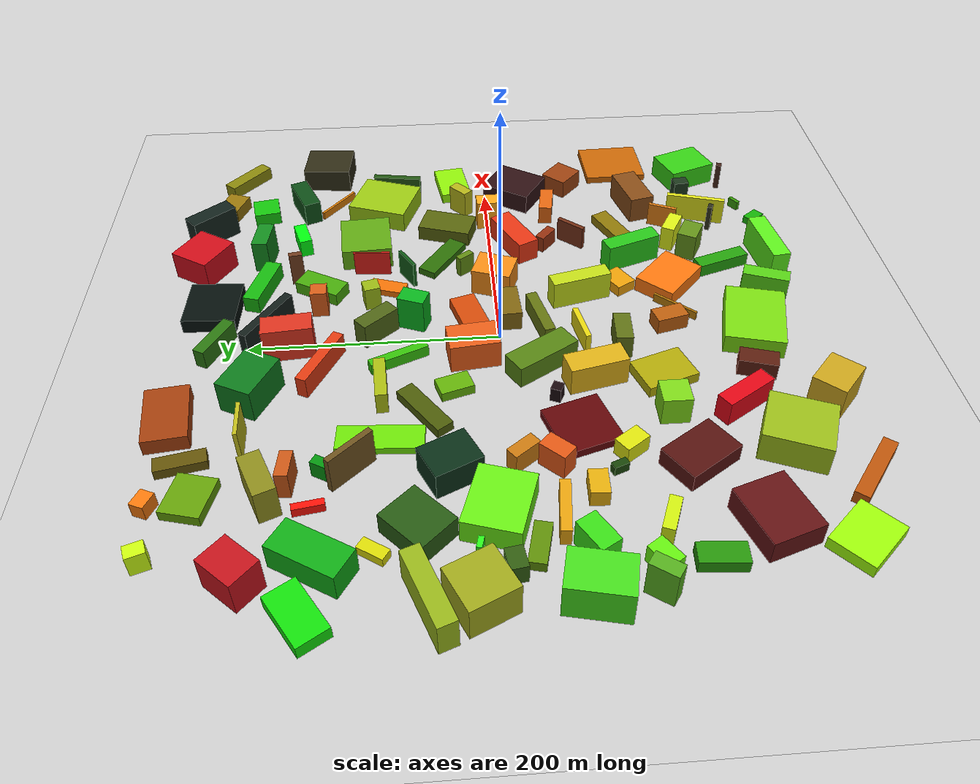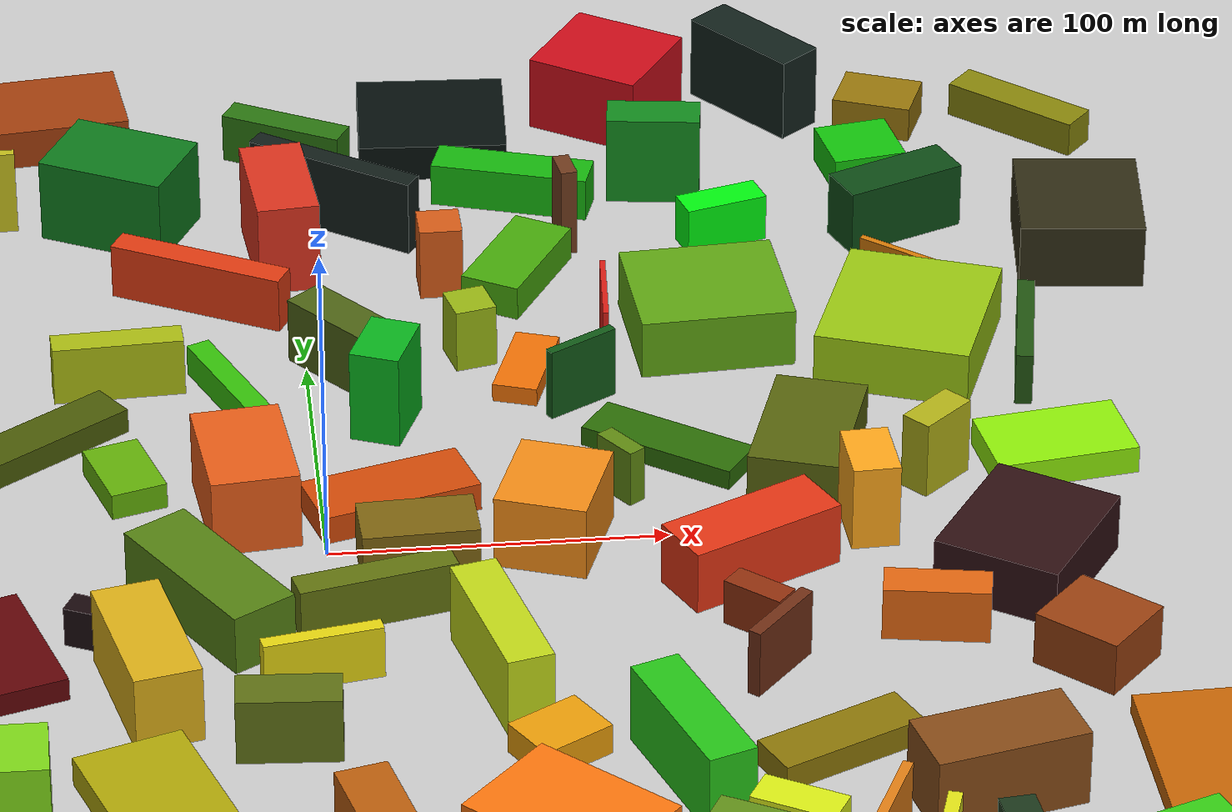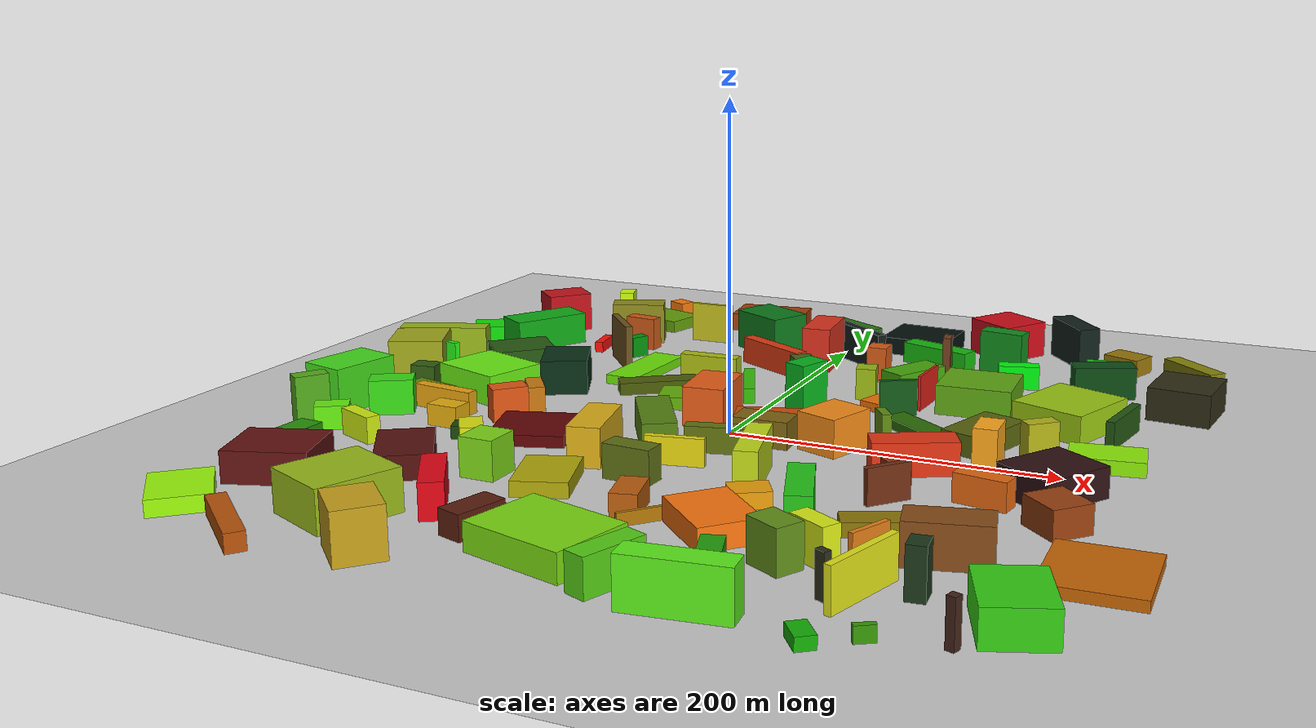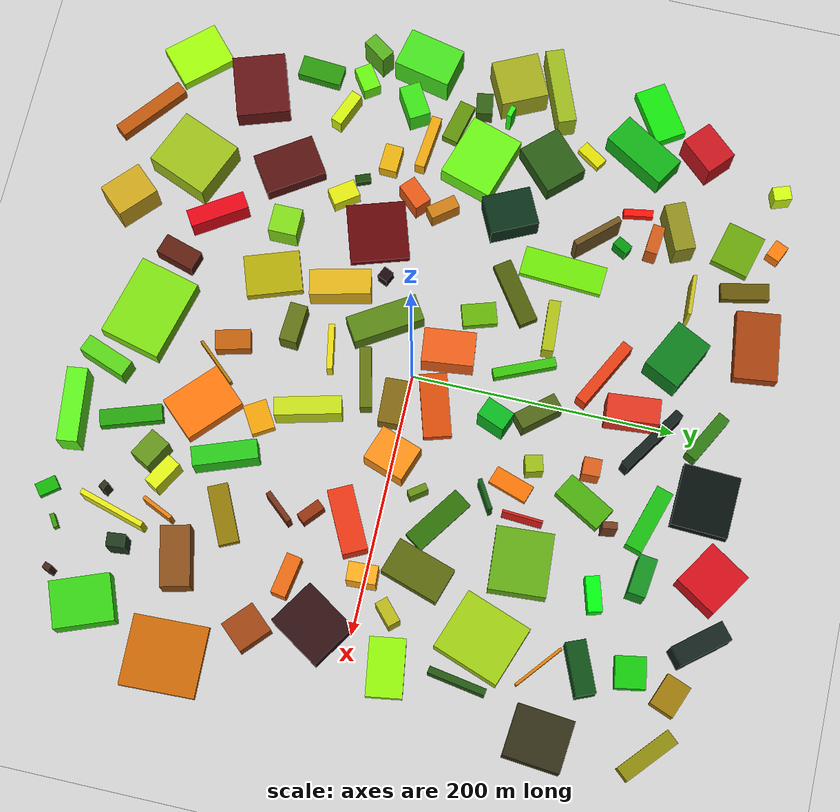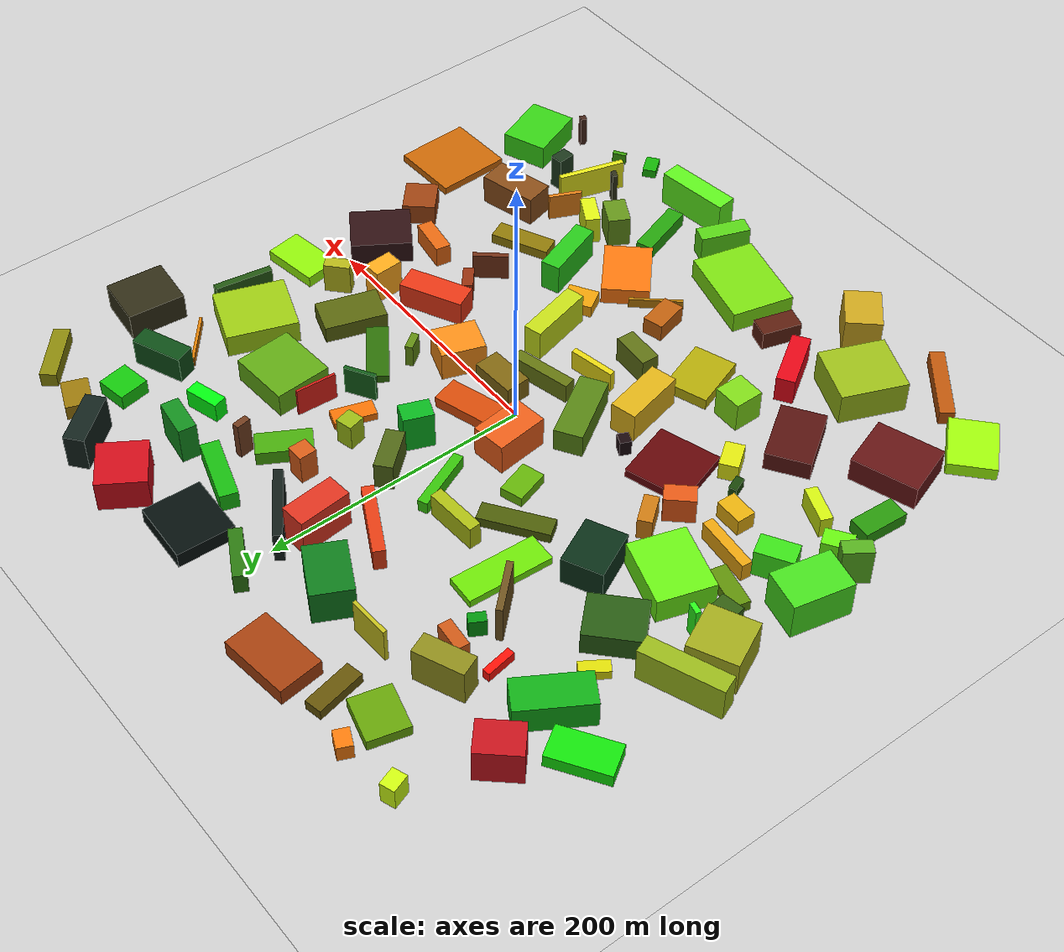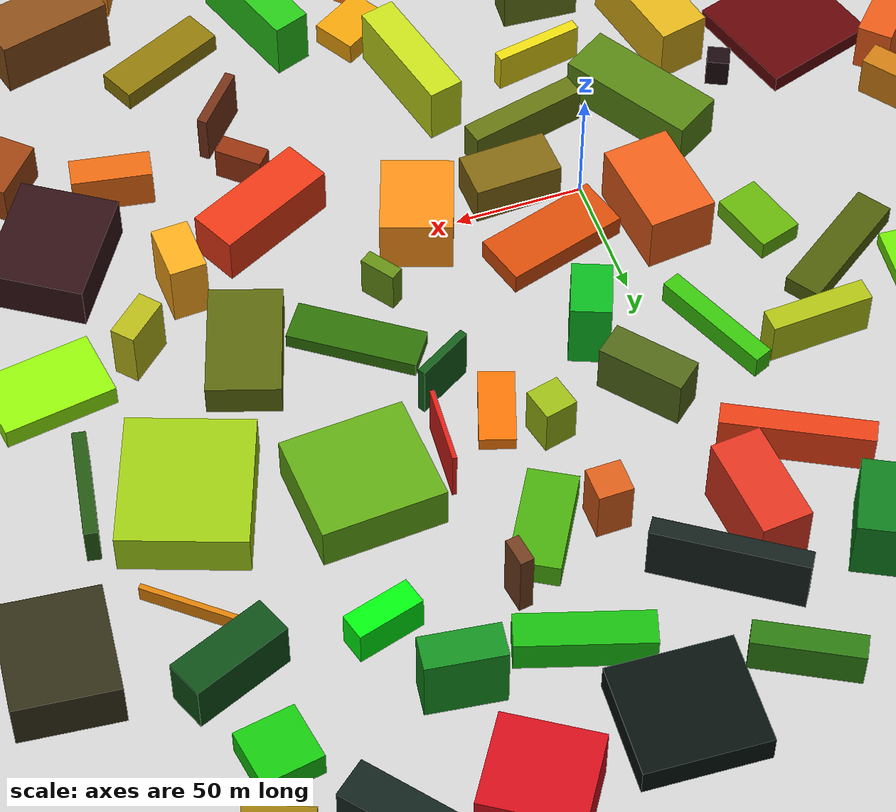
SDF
<sdf version='1.6'>
  <world name='default'>
    <light name='sun' type='directional'>
      <cast_shadows>1</cast_shadows>
      <pose frame=''>0 0 10 0 -0 0</pose>
      <diffuse>0.8 0.8 0.8 1</diffuse>
      <specular>0.2 0.2 0.2 1</specular>
      <attenuation>
        <range>1000</range>
        <constant>0.9</constant>
        <linear>0.01</linear>
        <quadratic>0.001</quadratic>
      </attenuation>
      <direction>-0.5 0.1 -0.9</direction>
    </light>
    <model name='ground_plane'>
      <static>1</static>
      <link name='link'>
        <collision name='collision'>
          <geometry>
            <plane>
              <normal>0 0 1</normal>
              <size>1090 1090</size>
            </plane>
          </geometry>
          <surface>
            <contact>
              <collide_bitmask>65535</collide_bitmask>
              <ode/>
            </contact>
            <friction>
              <ode>
                <mu>100</mu>
                <mu2>50</mu2>
              </ode>
              <torsional>
                <ode/>
              </torsional>
            </friction>
            <bounce/>
          </surface>
          <max_contacts>100</max_contacts>
        </collision>
        <visual name='visual'>
          <cast_shadows>0</cast_shadows>
          <geometry>
            <plane>
              <normal>0 0 1</normal>
              <size>1090 1090</size>
            </plane>
          </geometry>
          <material>
            <script>
              <uri>file://media/materials/scripts/gazebo.material</uri>
              <name>Gazebo/Grey</name>
            </script>
          </material>
        </visual>
        <self_collide>0</self_collide>
        <enable_wind>0</enable_wind>
        <kinematic>0</kinematic>
      </link>
    </model>
    <gravity>0 0 -9.8</gravity>
    <magnetic_field>6e-06 2.3e-05 -4.2e-05</magnetic_field>
    <atmosphere type='adiabatic'/>
    <physics name='default_physics' default='0' type='ode'>
      <max_step_size>0.001</max_step_size>
      <real_time_factor>1</real_time_factor>
      <real_time_update_rate>1000</real_time_update_rate>
    </physics>
    <scene>
      <ambient>0.4 0.4 0.4 1</ambient>
      <background>0.7 0.7 0.7 1</background>
      <shadows>1</shadows>
    </scene>
    <audio>
      <device>default</device>
    </audio>
    <wind/>
    <spherical_coordinates>
      <surface_model>EARTH_WGS84</surface_model>
      <latitude_deg>0</latitude_deg>
      <longitude_deg>0</longitude_deg>
      <elevation>0</elevation>
      <heading_deg>0</heading_deg>
    </spherical_coordinates>
    <model name='box_0'>
      <pose>11.0 98.0 10.67856067899134 0.0 0.0 -0.8694971052716423</pose>
      <link name='link'>
        <inertial>
          <mass>1</mass>
          <inertia>
            <ixx>1.0</ixx>
            <ixy>0</ixy>
            <ixz>0</ixz>
            <iyy>1.0</iyy>
            <iyz>0</iyz>
            <izz>1.0</izz>
          </inertia>
        </inertial>
        <collision name='collision'>
          <geometry>
            <box>
              <size>33.5071474526018 13.437500068040059 21.35712135798268</size>
            </box>
          </geometry>
          <max_contacts>100</max_contacts>
          <surface>
            <contact>
              <ode/>
            </contact>
            <bounce/>
            <friction>
              <torsional>
                <ode/>
              </torsional>
              <ode/>
            </friction>
          </surface>
        </collision>
        <visual name='visual'>
          <geometry>
            <box>
              <size>33.5071474526018 13.437500068040059 21.35712135798268</size>
            </box>
          </geometry>
          <material>
            <ambient>0.3059676274096351 0.3932885663509397 0.08375341709012817 1</ambient>
            <diffuse>0.3059676274096351 0.3932885663509397 0.08375341709012817 1</diffuse>
          </material>
        </visual>
        <self_collide>0</self_collide>
        <enable_wind>0</enable_wind>
        <kinematic>0</kinematic>
      </link>
    </model>
    <model name='box_1'>
      <pose>-30.0 140.0 8.917939824284897 0.0 0.0 -2.049125349434252</pose>
      <link name='link'>
        <inertial>
          <mass>1</mass>
          <inertia>
            <ixx>1.0</ixx>
            <ixy>0</ixy>
            <ixz>0</ixz>
            <iyy>1.0</iyy>
            <iyz>0</iyz>
            <izz>1.0</izz>
          </inertia>
        </inertial>
        <collision name='collision'>
          <geometry>
            <box>
              <size>8.75231158337338 56.50787311186727 17.835879648569794</size>
            </box>
          </geometry>
          <max_contacts>100</max_contacts>
          <surface>
            <contact>
              <ode/>
            </contact>
            <bounce/>
            <friction>
              <torsional>
                <ode/>
              </torsional>
              <ode/>
            </friction>
          </surface>
        </collision>
        <visual name='visual'>
          <geometry>
            <box>
              <size>8.75231158337338 56.50787311186727 17.835879648569794</size>
            </box>
          </geometry>
          <material>
            <ambient>0.8817718373286103 0.23068205831926336 0.06994462607282272 1</ambient>
            <diffuse>0.8817718373286103 0.23068205831926336 0.06994462607282272 1</diffuse>
          </material>
        </visual>
        <self_collide>0</self_collide>
        <enable_wind>0</enable_wind>
        <kinematic>0</kinematic>
      </link>
    </model>
    <model name='box_2'>
      <pose>-53.0 190.0 13.626873659348835 0.0 0.0 -0.46946448745551506</pose>
      <link name='link'>
        <inertial>
          <mass>1</mass>
          <inertia>
            <ixx>1.0</ixx>
            <ixy>0</ixy>
            <ixz>0</ixz>
            <iyy>1.0</iyy>
            <iyz>0</iyz>
            <izz>1.0</izz>
          </inertia>
        </inertial>
        <collision name='collision'>
          <geometry>
            <box>
              <size>41.11067537883807 29.60799992010874 27.25374731869767</size>
            </box>
          </geometry>
          <max_contacts>100</max_contacts>
          <surface>
            <contact>
              <ode/>
            </contact>
            <bounce/>
            <friction>
              <torsional>
                <ode/>
              </torsional>
              <ode/>
            </friction>
          </surface>
        </collision>
        <visual name='visual'>
          <geometry>
            <box>
              <size>41.11067537883807 29.60799992010874 27.25374731869767</size>
            </box>
          </geometry>
          <material>
            <ambient>0.051129619293508344 0.47694808917677767 0.10687744046548106 1</ambient>
            <diffuse>0.051129619293508344 0.47694808917677767 0.10687744046548106 1</diffuse>
          </material>
        </visual>
        <self_collide>0</self_collide>
        <enable_wind>0</enable_wind>
        <kinematic>0</kinematic>
      </link>
    </model>
    <model name='box_3'>
      <pose>200.0 -28.0 9.022767748040945 0.0 0.0 0.9989461405889835</pose>
      <link name='link'>
        <inertial>
          <mass>1</mass>
          <inertia>
            <ixx>1.0</ixx>
            <ixy>0</ixy>
            <ixz>0</ixz>
            <iyy>1.0</iyy>
            <iyz>0</iyz>
            <izz>1.0</izz>
          </inertia>
        </inertial>
        <collision name='collision'>
          <geometry>
            <box>
              <size>45.36900019797469 38.38082626452342 18.04553549608189</size>
            </box>
          </geometry>
          <max_contacts>100</max_contacts>
          <surface>
            <contact>
              <ode/>
            </contact>
            <bounce/>
            <friction>
              <torsional>
                <ode/>
              </torsional>
              <ode/>
            </friction>
          </surface>
        </collision>
        <visual name='visual'>
          <geometry>
            <box>
              <size>45.36900019797469 38.38082626452342 18.04553549608189</size>
            </box>
          </geometry>
          <material>
            <ambient>0.18105585911303934 0.06124740286496 0.0707668058669878 1</ambient>
            <diffuse>0.18105585911303934 0.06124740286496 0.0707668058669878 1</diffuse>
          </material>
        </visual>
        <self_collide>0</self_collide>
        <enable_wind>0</enable_wind>
        <kinematic>0</kinematic>
      </link>
    </model>
    <model name='box_4'>
      <pose>-54.0 -68.0 11.932399481538145 0.0 0.0 -1.3448074982335059</pose>
      <link name='link'>
        <inertial>
          <mass>1</mass>
          <inertia>
            <ixx>1.0</ixx>
            <ixy>0</ixy>
            <ixz>0</ixz>
            <iyy>1.0</iyy>
            <iyz>0</iyz>
            <izz>1.0</izz>
          </inertia>
        </inertial>
        <collision name='collision'>
          <geometry>
            <box>
              <size>46.50718704877159 19.704099781383178 23.86479896307629</size>
            </box>
          </geometry>
          <max_contacts>100</max_contacts>
          <surface>
            <contact>
              <ode/>
            </contact>
            <bounce/>
            <friction>
              <torsional>
                <ode/>
              </torsional>
              <ode/>
            </friction>
          </surface>
        </collision>
        <visual name='visual'>
          <geometry>
            <box>
              <size>46.50718704877159 19.704099781383178 23.86479896307629</size>
            </box>
          </geometry>
          <material>
            <ambient>0.8671601061280931 0.6890520242899425 0.09358744691402467 1</ambient>
            <diffuse>0.8671601061280931 0.6890520242899425 0.09358744691402467 1</diffuse>
          </material>
        </visual>
        <self_collide>0</self_collide>
        <enable_wind>0</enable_wind>
        <kinematic>0</kinematic>
      </link>
    </model>
    <model name='box_5'>
      <pose>93.0 -120.0 12.180641677544292 0.0 0.0 0.3478907333555959</pose>
      <link name='link'>
        <inertial>
          <mass>1</mass>
          <inertia>
            <ixx>1.0</ixx>
            <ixy>0</ixy>
            <ixz>0</ixz>
            <iyy>1.0</iyy>
            <iyz>0</iyz>
            <izz>1.0</izz>
          </inertia>
        </inertial>
        <collision name='collision'>
          <geometry>
            <box>
              <size>14.568717129107444 48.8070347128669 24.361283355088585</size>
            </box>
          </geometry>
          <max_contacts>100</max_contacts>
          <surface>
            <contact>
              <ode/>
            </contact>
            <bounce/>
            <friction>
              <torsional>
                <ode/>
              </torsional>
              <ode/>
            </friction>
          </surface>
        </collision>
        <visual name='visual'>
          <geometry>
            <box>
              <size>14.568717129107444 48.8070347128669 24.361283355088585</size>
            </box>
          </geometry>
          <material>
            <ambient>0.1510670350167691 0.7726870333516273 0.09553444452975915 1</ambient>
            <diffuse>0.1510670350167691 0.7726870333516273 0.09553444452975915 1</diffuse>
          </material>
        </visual>
        <self_collide>0</self_collide>
        <enable_wind>0</enable_wind>
        <kinematic>0</kinematic>
      </link>
    </model>
    <model name='box_6'>
      <pose>-130.0 -201.0 12.420439109522807 0.0 0.0 2.746577244491435</pose>
      <link name='link'>
        <inertial>
          <mass>1</mass>
          <inertia>
            <ixx>1.0</ixx>
            <ixy>0</ixy>
            <ixz>0</ixz>
            <iyy>1.0</iyy>
            <iyz>0</iyz>
            <izz>1.0</izz>
          </inertia>
        </inertial>
        <collision name='collision'>
          <geometry>
            <box>
              <size>45.535640340912956 49.55207788775828 24.840878219045614</size>
            </box>
          </geometry>
          <max_contacts>100</max_contacts>
          <surface>
            <contact>
              <ode/>
            </contact>
            <bounce/>
            <friction>
              <torsional>
                <ode/>
              </torsional>
              <ode/>
            </friction>
          </surface>
        </collision>
        <visual name='visual'>
          <geometry>
            <box>
              <size>45.535640340912956 49.55207788775828 24.840878219045614</size>
            </box>
          </geometry>
          <material>
            <ambient>0.6061634778335582 0.7349553700921742 0.09741520870213966 1</ambient>
            <diffuse>0.6061634778335582 0.7349553700921742 0.09741520870213966 1</diffuse>
          </material>
        </visual>
        <self_collide>0</self_collide>
        <enable_wind>0</enable_wind>
        <kinematic>0</kinematic>
      </link>
    </model>
    <model name='box_7'>
      <pose>-178.0 14.0 9.835916674045993 0.0 0.0 2.831345659289908</pose>
      <link name='link'>
        <inertial>
          <mass>1</mass>
          <inertia>
            <ixx>1.0</ixx>
            <ixy>0</ixy>
            <ixz>0</ixz>
            <iyy>1.0</iyy>
            <iyz>0</iyz>
            <izz>1.0</izz>
          </inertia>
        </inertial>
        <collision name='collision'>
          <geometry>
            <box>
              <size>51.042119715471564 41.800423260667934 19.671833348091987</size>
            </box>
          </geometry>
          <max_contacts>100</max_contacts>
          <surface>
            <contact>
              <ode/>
            </contact>
            <bounce/>
            <friction>
              <torsional>
                <ode/>
              </torsional>
              <ode/>
            </friction>
          </surface>
        </collision>
        <visual name='visual'>
          <geometry>
            <box>
              <size>51.042119715471564 41.800423260667934 19.671833348091987</size>
            </box>
          </geometry>
          <material>
            <ambient>0.41294661639301333 0.9355164949211463 0.07714444450232151 1</ambient>
            <diffuse>0.41294661639301333 0.9355164949211463 0.07714444450232151 1</diffuse>
          </material>
        </visual>
        <self_collide>0</self_collide>
        <enable_wind>0</enable_wind>
        <kinematic>0</kinematic>
      </link>
    </model>
    <model name='box_8'>
      <pose>-93.0 -120.0 11.785225408232899 0.0 0.0 -1.575943027175118</pose>
      <link name='link'>
        <inertial>
          <mass>1</mass>
          <inertia>
            <ixx>1.0</ixx>
            <ixy>0</ixy>
            <ixz>0</ixz>
            <iyy>1.0</iyy>
            <iyz>0</iyz>
            <izz>1.0</izz>
          </inertia>
        </inertial>
        <collision name='collision'>
          <geometry>
            <box>
              <size>21.993526169065415 21.63359584731483 23.570450816465797</size>
            </box>
          </geometry>
          <max_contacts>100</max_contacts>
          <surface>
            <contact>
              <ode/>
            </contact>
            <bounce/>
            <friction>
              <torsional>
                <ode/>
              </torsional>
              <ode/>
            </friction>
          </surface>
        </collision>
        <visual name='visual'>
          <geometry>
            <box>
              <size>21.993526169065415 21.63359584731483 23.570450816465797</size>
            </box>
          </geometry>
          <material>
            <ambient>0.4954918938201597 0.844533946746231 0.09243314045672861 1</ambient>
            <diffuse>0.4954918938201597 0.844533946746231 0.09243314045672861 1</diffuse>
          </material>
        </visual>
        <self_collide>0</self_collide>
        <enable_wind>0</enable_wind>
        <kinematic>0</kinematic>
      </link>
    </model>
    <model name='box_9'>
      <pose>-164.0 -246.0 5.328805302925539 0.0 0.0 0.8906002371310532</pose>
      <link name='link'>
        <inertial>
          <mass>1</mass>
          <inertia>
            <ixx>1.0</ixx>
            <ixy>0</ixy>
            <ixz>0</ixz>
            <iyy>1.0</iyy>
            <iyz>0</iyz>
            <izz>1.0</izz>
          </inertia>
        </inertial>
        <collision name='collision'>
          <geometry>
            <box>
              <size>10.84539500023051 59.44293036375359 10.657610605851078</size>
            </box>
          </geometry>
          <max_contacts>100</max_contacts>
          <surface>
            <contact>
              <ode/>
            </contact>
            <bounce/>
            <friction>
              <torsional>
                <ode/>
              </torsional>
              <ode/>
            </friction>
          </surface>
        </collision>
        <visual name='visual'>
          <geometry>
            <box>
              <size>10.84539500023051 59.44293036375359 10.657610605851078</size>
            </box>
          </geometry>
          <material>
            <ambient>0.732964302147717 0.3321250497890862 0.04179455139549442 1</ambient>
            <diffuse>0.732964302147717 0.3321250497890862 0.04179455139549442 1</diffuse>
          </material>
        </visual>
        <self_collide>0</self_collide>
        <enable_wind>0</enable_wind>
        <kinematic>0</kinematic>
      </link>
    </model>
    <model name='box_10'>
      <pose>218.0 30.0 4.36076915369778 0.0 0.0 1.7217781965595014</pose>
      <link name='link'>
        <inertial>
          <mass>1</mass>
          <inertia>
            <ixx>1.0</ixx>
            <ixy>0</ixy>
            <ixz>0</ixz>
            <iyy>1.0</iyy>
            <iyz>0</iyz>
            <izz>1.0</izz>
          </inertia>
        </inertial>
        <collision name='collision'>
          <geometry>
            <box>
              <size>26.88339719535763 43.408110691959145 8.72153830739556</size>
            </box>
          </geometry>
          <max_contacts>100</max_contacts>
          <surface>
            <contact>
              <ode/>
            </contact>
            <bounce/>
            <friction>
              <torsional>
                <ode/>
              </torsional>
              <ode/>
            </friction>
          </surface>
        </collision>
        <visual name='visual'>
          <geometry>
            <box>
              <size>26.88339719535763 43.408110691959145 8.72153830739556</size>
            </box>
          </geometry>
          <material>
            <ambient>0.5631429183391052 0.9368762787943058 0.034202111009394354 1</ambient>
            <diffuse>0.5631429183391052 0.9368762787943058 0.034202111009394354 1</diffuse>
          </material>
        </visual>
        <self_collide>0</self_collide>
        <enable_wind>0</enable_wind>
        <kinematic>0</kinematic>
      </link>
    </model>
    <model name='box_11'>
      <pose>-35.0 -29.0 9.268477076665707 0.0 0.0 0.5589204189226971</pose>
      <link name='link'>
        <inertial>
          <mass>1</mass>
          <inertia>
            <ixx>1.0</ixx>
            <ixy>0</ixy>
            <ixz>0</ixz>
            <iyy>1.0</iyy>
            <iyz>0</iyz>
            <izz>1.0</izz>
          </inertia>
        </inertial>
        <collision name='collision'>
          <geometry>
            <box>
              <size>20.73823721204666 55.10534166336652 18.536954153331415</size>
            </box>
          </geometry>
          <max_contacts>100</max_contacts>
          <surface>
            <contact>
              <ode/>
            </contact>
            <bounce/>
            <friction>
              <torsional>
                <ode/>
              </torsional>
              <ode/>
            </friction>
          </surface>
        </collision>
        <visual name='visual'>
          <geometry>
            <box>
              <size>20.73823721204666 55.10534166336652 18.536954153331415</size>
            </box>
          </geometry>
          <material>
            <ambient>0.33461857477396406 0.5110184405610818 0.07269393785620162 1</ambient>
            <diffuse>0.33461857477396406 0.5110184405610818 0.07269393785620162 1</diffuse>
          </material>
        </visual>
        <self_collide>0</self_collide>
        <enable_wind>0</enable_wind>
        <kinematic>0</kinematic>
      </link>
    </model>
    <model name='box_12'>
      <pose>244.0 147.0 10.400552500799233 0.0 0.0 3.0447985492003213</pose>
      <link name='link'>
        <inertial>
          <mass>1</mass>
          <inertia>
            <ixx>1.0</ixx>
            <ixy>0</ixy>
            <ixz>0</ixz>
            <iyy>1.0</iyy>
            <iyz>0</iyz>
            <izz>1.0</izz>
          </inertia>
        </inertial>
        <collision name='collision'>
          <geometry>
            <box>
              <size>38.614115217144985 42.638338753852224 20.801105001598465</size>
            </box>
          </geometry>
          <max_contacts>100</max_contacts>
          <surface>
            <contact>
              <ode/>
            </contact>
            <bounce/>
            <friction>
              <torsional>
                <ode/>
              </torsional>
              <ode/>
            </friction>
          </surface>
        </collision>
        <visual name='visual'>
          <geometry>
            <box>
              <size>38.614115217144985 42.638338753852224 20.801105001598465</size>
            </box>
          </geometry>
          <material>
            <ambient>0.18408507084050296 0.17183968187200183 0.08157296079058221 1</ambient>
            <diffuse>0.18408507084050296 0.17183968187200183 0.08157296079058221 1</diffuse>
          </material>
        </visual>
        <self_collide>0</self_collide>
        <enable_wind>0</enable_wind>
        <kinematic>0</kinematic>
      </link>
    </model>
    <model name='box_13'>
      <pose>-141.0 -129.0 7.3939138019333015 0.0 0.0 0.583486950459746</pose>
      <link name='link'>
        <inertial>
          <mass>1</mass>
          <inertia>
            <ixx>1.0</ixx>
            <ixy>0</ixy>
            <ixz>0</ixz>
            <iyy>1.0</iyy>
            <iyz>0</iyz>
            <izz>1.0</izz>
          </inertia>
        </inertial>
        <collision name='collision'>
          <geometry>
            <box>
              <size>32.49622416145748 47.534398894730714 14.787827603866603</size>
            </box>
          </geometry>
          <max_contacts>100</max_contacts>
          <surface>
            <contact>
              <ode/>
            </contact>
            <bounce/>
            <friction>
              <torsional>
                <ode/>
              </torsional>
              <ode/>
            </friction>
          </surface>
        </collision>
        <visual name='visual'>
          <geometry>
            <box>
              <size>32.49622416145748 47.534398894730714 14.787827603866603</size>
            </box>
          </geometry>
          <material>
            <ambient>0.3330033309653926 0.07084292728000297 0.05799148079947687 1</ambient>
            <diffuse>0.3330033309653926 0.07084292728000297 0.05799148079947687 1</diffuse>
          </material>
        </visual>
        <self_collide>0</self_collide>
        <enable_wind>0</enable_wind>
        <kinematic>0</kinematic>
      </link>
    </model>
    <model name='box_14'>
      <pose>102.0 -174.0 12.236211449478962 0.0 0.0 -2.0681476778430423</pose>
      <link name='link'>
        <inertial>
          <mass>1</mass>
          <inertia>
            <ixx>1.0</ixx>
            <ixy>0</ixy>
            <ixz>0</ixz>
            <iyy>1.0</iyy>
            <iyz>0</iyz>
            <izz>1.0</izz>
          </inertia>
        </inertial>
        <collision name='collision'>
          <geometry>
            <box>
              <size>16.761458297277493 23.171178610230232 24.472422898957923</size>
            </box>
          </geometry>
          <max_contacts>100</max_contacts>
          <surface>
            <contact>
              <ode/>
            </contact>
            <bounce/>
            <friction>
              <torsional>
                <ode/>
              </torsional>
              <ode/>
            </friction>
          </surface>
        </collision>
        <visual name='visual'>
          <geometry>
            <box>
              <size>16.761458297277493 23.171178610230232 24.472422898957923</size>
            </box>
          </geometry>
          <material>
            <ambient>0.38638441571702364 0.569032718956029 0.09597028587826636 1</ambient>
            <diffuse>0.38638441571702364 0.569032718956029 0.09597028587826636 1</diffuse>
          </material>
        </visual>
        <self_collide>0</self_collide>
        <enable_wind>0</enable_wind>
        <kinematic>0</kinematic>
      </link>
    </model>
    <model name='box_15'>
      <pose>-196.0 -97.0 8.17357476078345 0.0 0.0 2.758787207787016</pose>
      <link name='link'>
        <inertial>
          <mass>1</mass>
          <inertia>
            <ixx>1.0</ixx>
            <ixy>0</ixy>
            <ixz>0</ixz>
            <iyy>1.0</iyy>
            <iyz>0</iyz>
            <izz>1.0</izz>
          </inertia>
        </inertial>
        <collision name='collision'>
          <geometry>
            <box>
              <size>28.291167822034396 8.949187133292341 16.3471495215669</size>
            </box>
          </geometry>
          <max_contacts>100</max_contacts>
          <surface>
            <contact>
              <ode/>
            </contact>
            <bounce/>
            <friction>
              <torsional>
                <ode/>
              </torsional>
              <ode/>
            </friction>
          </surface>
        </collision>
        <visual name='visual'>
          <geometry>
            <box>
              <size>28.291167822034396 8.949187133292341 16.3471495215669</size>
            </box>
          </geometry>
          <material>
            <ambient>0.8156770872116239 0.9296706031716788 0.06410646871202706 1</ambient>
            <diffuse>0.8156770872116239 0.9296706031716788 0.06410646871202706 1</diffuse>
          </material>
        </visual>
        <self_collide>0</self_collide>
        <enable_wind>0</enable_wind>
        <kinematic>0</kinematic>
      </link>
    </model>
    <model name='box_16'>
      <pose>12.0 -33.0 7.8999495172870144 0.0 0.0 -2.9074084649632392</pose>
      <link name='link'>
        <inertial>
          <mass>1</mass>
          <inertia>
            <ixx>1.0</ixx>
            <ixy>0</ixy>
            <ixz>0</ixz>
            <iyy>1.0</iyy>
            <iyz>0</iyz>
            <izz>1.0</izz>
          </inertia>
        </inertial>
        <collision name='collision'>
          <geometry>
            <box>
              <size>47.22595043230734 8.998547996909277 15.799899034574029</size>
            </box>
          </geometry>
          <max_contacts>100</max_contacts>
          <surface>
            <contact>
              <ode/>
            </contact>
            <bounce/>
            <friction>
              <torsional>
                <ode/>
              </torsional>
              <ode/>
            </friction>
          </surface>
        </collision>
        <visual name='visual'>
          <geometry>
            <box>
              <size>47.22595043230734 8.998547996909277 15.799899034574029</size>
            </box>
          </geometry>
          <material>
            <ambient>0.386585925612677 0.4516583894784828 0.06196038837087854 1</ambient>
            <diffuse>0.386585925612677 0.4516583894784828 0.06196038837087854 1</diffuse>
          </material>
        </visual>
        <self_collide>0</self_collide>
        <enable_wind>0</enable_wind>
        <kinematic>0</kinematic>
      </link>
    </model>
    <model name='box_17'>
      <pose>20.0 22.0 4.452574775439398 0.0 0.0 0.2918054289695745</pose>
      <link name='link'>
        <inertial>
          <mass>1</mass>
          <inertia>
            <ixx>1.0</ixx>
            <ixy>0</ixy>
            <ixz>0</ixz>
            <iyy>1.0</iyy>
            <iyz>0</iyz>
            <izz>1.0</izz>
          </inertia>
        </inertial>
        <collision name='collision'>
          <geometry>
            <box>
              <size>49.000109454054865 21.082333981721092 8.905149550878797</size>
            </box>
          </geometry>
          <max_contacts>100</max_contacts>
          <surface>
            <contact>
              <ode/>
            </contact>
            <bounce/>
            <friction>
              <torsional>
                <ode/>
              </torsional>
              <ode/>
            </friction>
          </surface>
        </collision>
        <visual name='visual'>
          <geometry>
            <box>
              <size>49.000109454054865 21.082333981721092 8.905149550878797</size>
            </box>
          </geometry>
          <material>
            <ambient>0.8293685395352113 0.29114021774623766 0.034922155101485476 1</ambient>
            <diffuse>0.8293685395352113 0.29114021774623766 0.034922155101485476 1</diffuse>
          </material>
        </visual>
        <self_collide>0</self_collide>
        <enable_wind>0</enable_wind>
        <kinematic>0</kinematic>
      </link>
    </model>
    <model name='box_18'>
      <pose>-105.0 -51.0 3.57855578145893 0.0 0.0 1.8775600879269823</pose>
      <link name='link'>
        <inertial>
          <mass>1</mass>
          <inertia>
            <ixx>1.0</ixx>
            <ixy>0</ixy>
            <ixz>0</ixz>
            <iyy>1.0</iyy>
            <iyz>0</iyz>
            <izz>1.0</izz>
          </inertia>
        </inertial>
        <collision name='collision'>
          <geometry>
            <box>
              <size>45.590993328448384 46.32370326211496 7.15711156291786</size>
            </box>
          </geometry>
          <max_contacts>100</max_contacts>
          <surface>
            <contact>
              <ode/>
            </contact>
            <bounce/>
            <friction>
              <torsional>
                <ode/>
              </torsional>
              <ode/>
            </friction>
          </surface>
        </collision>
        <visual name='visual'>
          <geometry>
            <box>
              <size>45.590993328448384 46.32370326211496 7.15711156291786</size>
            </box>
          </geometry>
          <material>
            <ambient>0.3803106719996403 0.016722689660681245 0.028067104168305334 1</ambient>
            <diffuse>0.3803106719996403 0.016722689660681245 0.028067104168305334 1</diffuse>
          </material>
        </visual>
        <self_collide>0</self_collide>
        <enable_wind>0</enable_wind>
        <kinematic>0</kinematic>
      </link>
    </model>
    <model name='box_19'>
      <pose>-16.0 -95.0 10.220430348067152 0.0 0.0 -0.05964402914281683</pose>
      <link name='link'>
        <inertial>
          <mass>1</mass>
          <inertia>
            <ixx>1.0</ixx>
            <ixy>0</ixy>
            <ixz>0</ixz>
            <iyy>1.0</iyy>
            <iyz>0</iyz>
            <izz>1.0</izz>
          </inertia>
        </inertial>
        <collision name='collision'>
          <geometry>
            <box>
              <size>29.72694537108584 13.459983994354998 20.440860696134305</size>
            </box>
          </geometry>
          <max_contacts>100</max_contacts>
          <surface>
            <contact>
              <ode/>
            </contact>
            <bounce/>
            <friction>
              <torsional>
                <ode/>
              </torsional>
              <ode/>
            </friction>
          </surface>
        </collision>
        <visual name='visual'>
          <geometry>
            <box>
              <size>29.72694537108584 13.459983994354998 20.440860696134305</size>
            </box>
          </geometry>
          <material>
            <ambient>0.3693755184638634 0.4395482027466472 0.0801602380240561 1</ambient>
            <diffuse>0.3693755184638634 0.4395482027466472 0.0801602380240561 1</diffuse>
          </material>
        </visual>
        <self_collide>0</self_collide>
        <enable_wind>0</enable_wind>
        <kinematic>0</kinematic>
      </link>
    </model>
    <model name='box_20'>
      <pose>183.0 93.0 8.946816165260138 0.0 0.0 -0.34660458879755934</pose>
      <link name='link'>
        <inertial>
          <mass>1</mass>
          <inertia>
            <ixx>1.0</ixx>
            <ixy>0</ixy>
            <ixz>0</ixz>
            <iyy>1.0</iyy>
            <iyz>0</iyz>
            <izz>1.0</izz>
          </inertia>
        </inertial>
        <collision name='collision'>
          <geometry>
            <box>
              <size>47.430815665113364 52.51957210905458 17.893632330520276</size>
            </box>
          </geometry>
          <max_contacts>100</max_contacts>
          <surface>
            <contact>
              <ode/>
            </contact>
            <bounce/>
            <friction>
              <torsional>
                <ode/>
              </torsional>
              <ode/>
            </friction>
          </surface>
        </collision>
        <visual name='visual'>
          <geometry>
            <box>
              <size>47.430815665113364 52.51957210905458 17.893632330520276</size>
            </box>
          </geometry>
          <material>
            <ambient>0.6064786898915688 0.780767434220349 0.07017110717851088 1</ambient>
            <diffuse>0.6064786898915688 0.780767434220349 0.07017110717851088 1</diffuse>
          </material>
        </visual>
        <self_collide>0</self_collide>
        <enable_wind>0</enable_wind>
        <kinematic>0</kinematic>
      </link>
    </model>
    <model name='box_21'>
      <pose>68.0 145.0 5.506815892541878 0.0 0.0 1.0504982057027636</pose>
      <link name='link'>
        <inertial>
          <mass>1</mass>
          <inertia>
            <ixx>1.0</ixx>
            <ixy>0</ixy>
            <ixz>0</ixz>
            <iyy>1.0</iyy>
            <iyz>0</iyz>
            <izz>1.0</izz>
          </inertia>
        </inertial>
        <collision name='collision'>
          <geometry>
            <box>
              <size>39.91934967818939 18.945758763937253 11.013631785083756</size>
            </box>
          </geometry>
          <max_contacts>100</max_contacts>
          <surface>
            <contact>
              <ode/>
            </contact>
            <bounce/>
            <friction>
              <torsional>
                <ode/>
              </torsional>
              <ode/>
            </friction>
          </surface>
        </collision>
        <visual name='visual'>
          <geometry>
            <box>
              <size>39.91934967818939 18.945758763937253 11.013631785083756</size>
            </box>
          </geometry>
          <material>
            <ambient>0.27681154281509324 0.6641535544460366 0.0431907128826814 1</ambient>
            <diffuse>0.27681154281509324 0.6641535544460366 0.0431907128826814 1</diffuse>
          </material>
        </visual>
        <self_collide>0</self_collide>
        <enable_wind>0</enable_wind>
        <kinematic>0</kinematic>
      </link>
    </model>
    <model name='box_22'>
      <pose>106.0 246.0 12.321171566801386 0.0 0.0 -0.5682716648869991</pose>
      <link name='link'>
        <inertial>
          <mass>1</mass>
          <inertia>
            <ixx>1.0</ixx>
            <ixy>0</ixy>
            <ixz>0</ixz>
            <iyy>1.0</iyy>
            <iyz>0</iyz>
            <izz>1.0</izz>
          </inertia>
        </inertial>
        <collision name='collision'>
          <geometry>
            <box>
              <size>37.347761429379275 35.48738556221239 24.642343133602772</size>
            </box>
          </geometry>
          <max_contacts>100</max_contacts>
          <surface>
            <contact>
              <ode/>
            </contact>
            <bounce/>
            <friction>
              <torsional>
                <ode/>
              </torsional>
              <ode/>
            </friction>
          </surface>
        </collision>
        <visual name='visual'>
          <geometry>
            <box>
              <size>37.347761429379275 35.48738556221239 24.642343133602772</size>
            </box>
          </geometry>
          <material>
            <ambient>0.8087825948908098 0.04922039290385771 0.09663663973961871 1</ambient>
            <diffuse>0.8087825948908098 0.04922039290385771 0.09663663973961871 1</diffuse>
          </material>
        </visual>
        <self_collide>0</self_collide>
        <enable_wind>0</enable_wind>
        <kinematic>0</kinematic>
      </link>
    </model>
    <model name='box_23'>
      <pose>-199.0 -166.0 9.504518910273303 0.0 0.0 1.8939893462124235</pose>
      <link name='link'>
        <inertial>
          <mass>1</mass>
          <inertia>
            <ixx>1.0</ixx>
            <ixy>0</ixy>
            <ixz>0</ixz>
            <iyy>1.0</iyy>
            <iyz>0</iyz>
            <izz>1.0</izz>
          </inertia>
        </inertial>
        <collision name='collision'>
          <geometry>
            <box>
              <size>40.95194382159373 48.951772654198074 19.009037820546606</size>
            </box>
          </geometry>
          <max_contacts>100</max_contacts>
          <surface>
            <contact>
              <ode/>
            </contact>
            <bounce/>
            <friction>
              <torsional>
                <ode/>
              </torsional>
              <ode/>
            </friction>
          </surface>
        </collision>
        <visual name='visual'>
          <geometry>
            <box>
              <size>40.95194382159373 48.951772654198074 19.009037820546606</size>
            </box>
          </geometry>
          <material>
            <ambient>0.38695531870469224 0.07292859815211827 0.07454524635508473 1</ambient>
            <diffuse>0.38695531870469224 0.07292859815211827 0.07454524635508473 1</diffuse>
          </material>
        </visual>
        <self_collide>0</self_collide>
        <enable_wind>0</enable_wind>
        <kinematic>0</kinematic>
      </link>
    </model>
    <model name='box_24'>
      <pose>-106.0 94.0 3.036187016197399 0.0 0.0 1.509970487362236</pose>
      <link name='link'>
        <inertial>
          <mass>1</mass>
          <inertia>
            <ixx>1.0</ixx>
            <ixy>0</ixy>
            <ixz>0</ixz>
            <iyy>1.0</iyy>
            <iyz>0</iyz>
            <izz>1.0</izz>
          </inertia>
        </inertial>
        <collision name='collision'>
          <geometry>
            <box>
              <size>63.77746449783848 22.556646956915394 6.072374032394798</size>
            </box>
          </geometry>
          <max_contacts>100</max_contacts>
          <surface>
            <contact>
              <ode/>
            </contact>
            <bounce/>
            <friction>
              <torsional>
                <ode/>
              </torsional>
              <ode/>
            </friction>
          </surface>
        </collision>
        <visual name='visual'>
          <geometry>
            <box>
              <size>63.77746449783848 22.556646956915394 6.072374032394798</size>
            </box>
          </geometry>
          <material>
            <ambient>0.42595351238871304 0.8888574919655837 0.02381323149958744 1</ambient>
            <diffuse>0.42595351238871304 0.8888574919655837 0.02381323149958744 1</diffuse>
          </material>
        </visual>
        <self_collide>0</self_collide>
        <enable_wind>0</enable_wind>
        <kinematic>0</kinematic>
      </link>
    </model>
    <model name='box_25'>
      <pose>-200.0 245.0 8.73518252108833 0.0 0.0 -1.2315014391945382</pose>
      <link name='link'>
        <inertial>
          <mass>1</mass>
          <inertia>
            <ixx>1.0</ixx>
            <ixy>0</ixy>
            <ixz>0</ixz>
            <iyy>1.0</iyy>
            <iyz>0</iyz>
            <izz>1.0</izz>
          </inertia>
        </inertial>
        <collision name='collision'>
          <geometry>
            <box>
              <size>13.61798697724973 10.92907385401943 17.47036504217666</size>
            </box>
          </geometry>
          <max_contacts>100</max_contacts>
          <surface>
            <contact>
              <ode/>
            </contact>
            <bounce/>
            <friction>
              <torsional>
                <ode/>
              </torsional>
              <ode/>
            </friction>
          </surface>
        </collision>
        <visual name='visual'>
          <geometry>
            <box>
              <size>13.61798697724973 10.92907385401943 17.47036504217666</size>
            </box>
          </geometry>
          <material>
            <ambient>0.8027560728399181 0.9941952972409885 0.06851123545951632 1</ambient>
            <diffuse>0.8027560728399181 0.9941952972409885 0.06851123545951632 1</diffuse>
          </material>
        </visual>
        <self_collide>0</self_collide>
        <enable_wind>0</enable_wind>
        <kinematic>0</kinematic>
      </link>
    </model>
    <model name='box_26'>
      <pose>-183.0 -29.0 7.3030311145086815 0.0 0.0 -1.6752385755741377</pose>
      <link name='link'>
        <inertial>
          <mass>1</mass>
          <inertia>
            <ixx>1.0</ixx>
            <ixy>0</ixy>
            <ixz>0</ixz>
            <iyy>1.0</iyy>
            <iyz>0</iyz>
            <izz>1.0</izz>
          </inertia>
        </inertial>
        <collision name='collision'>
          <geometry>
            <box>
              <size>7.795190501975962 42.77033790904829 14.606062229017363</size>
            </box>
          </geometry>
          <max_contacts>100</max_contacts>
          <surface>
            <contact>
              <ode/>
            </contact>
            <bounce/>
            <friction>
              <torsional>
                <ode/>
              </torsional>
              <ode/>
            </friction>
          </surface>
        </collision>
        <visual name='visual'>
          <geometry>
            <box>
              <size>7.795190501975962 42.77033790904829 14.606062229017363</size>
            </box>
          </geometry>
          <material>
            <ambient>0.9105739579186616 0.6388018349689645 0.05727867540791123 1</ambient>
            <diffuse>0.9105739579186616 0.6388018349689645 0.05727867540791123 1</diffuse>
          </material>
        </visual>
        <self_collide>0</self_collide>
        <enable_wind>0</enable_wind>
        <kinematic>0</kinematic>
      </link>
    </model>
    <model name='box_27'>
      <pose>-210.0 135.0 10.913565074115308 0.0 0.0 -2.118815242038815</pose>
      <link name='link'>
        <inertial>
          <mass>1</mass>
          <inertia>
            <ixx>1.0</ixx>
            <ixy>0</ixy>
            <ixz>0</ixz>
            <iyy>1.0</iyy>
            <iyz>0</iyz>
            <izz>1.0</izz>
          </inertia>
        </inertial>
        <collision name='collision'>
          <geometry>
            <box>
              <size>53.27998433183104 24.81352422162694 21.827130148230616</size>
            </box>
          </geometry>
          <max_contacts>100</max_contacts>
          <surface>
            <contact>
              <ode/>
            </contact>
            <bounce/>
            <friction>
              <torsional>
                <ode/>
              </torsional>
              <ode/>
            </friction>
          </surface>
        </collision>
        <visual name='visual'>
          <geometry>
            <box>
              <size>53.27998433183104 24.81352422162694 21.827130148230616</size>
            </box>
          </geometry>
          <material>
            <ambient>0.06403537618711952 0.6784265041522384 0.08559658881659064 1</ambient>
            <diffuse>0.06403537618711952 0.6784265041522384 0.08559658881659064 1</diffuse>
          </material>
        </visual>
        <self_collide>0</self_collide>
        <enable_wind>0</enable_wind>
        <kinematic>0</kinematic>
      </link>
    </model>
    <model name='box_28'>
      <pose>-207.0 -10.0 4.231376765273415 0.0 0.0 1.3373384618519792</pose>
      <link name='link'>
        <inertial>
          <mass>1</mass>
          <inertia>
            <ixx>1.0</ixx>
            <ixy>0</ixy>
            <ixz>0</ixz>
            <iyy>1.0</iyy>
            <iyz>0</iyz>
            <izz>1.0</izz>
          </inertia>
        </inertial>
        <collision name='collision'>
          <geometry>
            <box>
              <size>12.646845841658484 33.043771107669194 8.46275353054683</size>
            </box>
          </geometry>
          <max_contacts>100</max_contacts>
          <surface>
            <contact>
              <ode/>
            </contact>
            <bounce/>
            <friction>
              <torsional>
                <ode/>
              </torsional>
              <ode/>
            </friction>
          </surface>
        </collision>
        <visual name='visual'>
          <geometry>
            <box>
              <size>12.646845841658484 33.043771107669194 8.46275353054683</size>
            </box>
          </geometry>
          <material>
            <ambient>0.3685038629019862 0.5590648833946542 0.033187268747242475 1</ambient>
            <diffuse>0.3685038629019862 0.5590648833946542 0.033187268747242475 1</diffuse>
          </material>
        </visual>
        <self_collide>0</self_collide>
        <enable_wind>0</enable_wind>
        <kinematic>0</kinematic>
      </link>
    </model>
    <model name='box_29'>
      <pose>238.0 225.0 5.6548939288473345 0.0 0.0 2.419468560276357</pose>
      <link name='link'>
        <inertial>
          <mass>1</mass>
          <inertia>
            <ixx>1.0</ixx>
            <ixy>0</ixy>
            <ixz>0</ixz>
            <iyy>1.0</iyy>
            <iyz>0</iyz>
            <izz>1.0</izz>
          </inertia>
        </inertial>
        <collision name='collision'>
          <geometry>
            <box>
              <size>45.80371317777055 12.001747961715667 11.309787857694669</size>
            </box>
          </geometry>
          <max_contacts>100</max_contacts>
          <surface>
            <contact>
              <ode/>
            </contact>
            <bounce/>
            <friction>
              <torsional>
                <ode/>
              </torsional>
              <ode/>
            </friction>
          </surface>
        </collision>
        <visual name='visual'>
          <geometry>
            <box>
              <size>45.80371317777055 12.001747961715667 11.309787857694669</size>
            </box>
          </geometry>
          <material>
            <ambient>0.5360395342016109 0.527621868070338 0.04435210924586145 1</ambient>
            <diffuse>0.5360395342016109 0.527621868070338 0.04435210924586145 1</diffuse>
          </material>
        </visual>
        <self_collide>0</self_collide>
        <enable_wind>0</enable_wind>
        <kinematic>0</kinematic>
      </link>
    </model>
    <model name='box_30'>
      <pose>203.0 -224.0 12.413508423237495 0.0 0.0 -0.32165454282165035</pose>
      <link name='link'>
        <inertial>
          <mass>1</mass>
          <inertia>
            <ixx>1.0</ixx>
            <ixy>0</ixy>
            <ixz>0</ixz>
            <iyy>1.0</iyy>
            <iyz>0</iyz>
            <izz>1.0</izz>
          </inertia>
        </inertial>
        <collision name='collision'>
          <geometry>
            <box>
              <size>4.813305103990317 4.957209498887963 24.82701684647499</size>
            </box>
          </geometry>
          <max_contacts>100</max_contacts>
          <surface>
            <contact>
              <ode/>
            </contact>
            <bounce/>
            <friction>
              <torsional>
                <ode/>
              </torsional>
              <ode/>
            </friction>
          </surface>
        </collision>
        <visual name='visual'>
          <geometry>
            <box>
              <size>4.813305103990317 4.957209498887963 24.82701684647499</size>
            </box>
          </geometry>
          <material>
            <ambient>0.26171214500727047 0.13915971177775255 0.0973608503783333 1</ambient>
            <diffuse>0.26171214500727047 0.13915971177775255 0.0973608503783333 1</diffuse>
          </material>
        </visual>
        <self_collide>0</self_collide>
        <enable_wind>0</enable_wind>
        <kinematic>0</kinematic>
      </link>
    </model>
    <model name='box_31'>
      <pose>104.0 43.0 3.1533066303083497 0.0 0.0 2.5326309119641586</pose>
      <link name='link'>
        <inertial>
          <mass>1</mass>
          <inertia>
            <ixx>1.0</ixx>
            <ixy>0</ixy>
            <ixz>0</ixz>
            <iyy>1.0</iyy>
            <iyz>0</iyz>
            <izz>1.0</izz>
          </inertia>
        </inertial>
        <collision name='collision'>
          <geometry>
            <box>
              <size>49.758344329735195 16.0046455354806 6.306613260616699</size>
            </box>
          </geometry>
          <max_contacts>100</max_contacts>
          <surface>
            <contact>
              <ode/>
            </contact>
            <bounce/>
            <friction>
              <torsional>
                <ode/>
              </torsional>
              <ode/>
            </friction>
          </surface>
        </collision>
        <visual name='visual'>
          <geometry>
            <box>
              <size>49.758344329735195 16.0046455354806 6.306613260616699</size>
            </box>
          </geometry>
          <material>
            <ambient>0.17324673085959463 0.4304662909968965 0.024731816708300783 1</ambient>
            <diffuse>0.17324673085959463 0.4304662909968965 0.024731816708300783 1</diffuse>
          </material>
        </visual>
        <self_collide>0</self_collide>
        <enable_wind>0</enable_wind>
        <kinematic>0</kinematic>
      </link>
    </model>
    <model name='box_32'>
      <pose>-164.0 141.0 3.691419895267824 0.0 0.0 1.7341141423958093</pose>
      <link name='link'>
        <inertial>
          <mass>1</mass>
          <inertia>
            <ixx>1.0</ixx>
            <ixy>0</ixy>
            <ixz>0</ixz>
            <iyy>1.0</iyy>
            <iyz>0</iyz>
            <izz>1.0</izz>
          </inertia>
        </inertial>
        <collision name='collision'>
          <geometry>
            <box>
              <size>22.68785350090937 5.627247254712298 7.382839790535648</size>
            </box>
          </geometry>
          <max_contacts>100</max_contacts>
          <surface>
            <contact>
              <ode/>
            </contact>
            <bounce/>
            <friction>
              <torsional>
                <ode/>
              </torsional>
              <ode/>
            </friction>
          </surface>
        </collision>
        <visual name='visual'>
          <geometry>
            <box>
              <size>22.68785350090937 5.627247254712298 7.382839790535648</size>
            </box>
          </geometry>
          <material>
            <ambient>0.9849376547672133 0.06906106926839817 0.028952312904061365 1</ambient>
            <diffuse>0.9849376547672133 0.06906106926839817 0.028952312904061365 1</diffuse>
          </material>
        </visual>
        <self_collide>0</self_collide>
        <enable_wind>0</enable_wind>
        <kinematic>0</kinematic>
      </link>
    </model>
    <model name='box_33'>
      <pose>22.0 68.0 14.940747189062463 0.0 0.0 2.7642369392400856</pose>
      <link name='link'>
        <inertial>
          <mass>1</mass>
          <inertia>
            <ixx>1.0</ixx>
            <ixy>0</ixy>
            <ixz>0</ixz>
            <iyy>1.0</iyy>
            <iyz>0</iyz>
            <izz>1.0</izz>
          </inertia>
        </inertial>
        <collision name='collision'>
          <geometry>
            <box>
              <size>15.324194474235277 22.052505184348746 29.881494378124927</size>
            </box>
          </geometry>
          <max_contacts>100</max_contacts>
          <surface>
            <contact>
              <ode/>
            </contact>
            <bounce/>
            <friction>
              <torsional>
                <ode/>
              </torsional>
              <ode/>
            </friction>
          </surface>
        </collision>
        <visual name='visual'>
          <geometry>
            <box>
              <size>15.324194474235277 22.052505184348746 29.881494378124927</size>
            </box>
          </geometry>
          <material>
            <ambient>0.03579773283249821 0.7024033259504372 0.11718233089460756 1</ambient>
            <diffuse>0.03579773283249821 0.7024033259504372 0.11718233089460756 1</diffuse>
          </material>
        </visual>
        <self_collide>0</self_collide>
        <enable_wind>0</enable_wind>
        <kinematic>0</kinematic>
      </link>
    </model>
    <model name='box_34'>
      <pose>175.0 -136.0 11.733812268122243 0.0 0.0 1.814076239464659</pose>
      <link name='link'>
        <inertial>
          <mass>1</mass>
          <inertia>
            <ixx>1.0</ixx>
            <ixy>0</ixy>
            <ixz>0</ixz>
            <iyy>1.0</iyy>
            <iyz>0</iyz>
            <izz>1.0</izz>
          </inertia>
        </inertial>
        <collision name='collision'>
          <geometry>
            <box>
              <size>22.131204064604418 44.93614656815169 23.467624536244486</size>
            </box>
          </geometry>
          <max_contacts>100</max_contacts>
          <surface>
            <contact>
              <ode/>
            </contact>
            <bounce/>
            <friction>
              <torsional>
                <ode/>
              </torsional>
              <ode/>
            </friction>
          </surface>
        </collision>
        <visual name='visual'>
          <geometry>
            <box>
              <size>22.131204064604418 44.93614656815169 23.467624536244486</size>
            </box>
          </geometry>
          <material>
            <ambient>0.5309834691382032 0.29794252185444836 0.09202990014213525 1</ambient>
            <diffuse>0.5309834691382032 0.29794252185444836 0.09202990014213525 1</diffuse>
          </material>
        </visual>
        <self_collide>0</self_collide>
        <enable_wind>0</enable_wind>
        <kinematic>0</kinematic>
      </link>
    </model>
    <model name='box_35'>
      <pose>213.0 -74.0 8.339446234318029 0.0 0.0 2.4051965561209148</pose>
      <link name='link'>
        <inertial>
          <mass>1</mass>
          <inertia>
            <ixx>1.0</ixx>
            <ixy>0</ixy>
            <ixz>0</ixz>
            <iyy>1.0</iyy>
            <iyz>0</iyz>
            <izz>1.0</izz>
          </inertia>
        </inertial>
        <collision name='collision'>
          <geometry>
            <box>
              <size>26.93304693015524 24.496622838593844 16.678892468636057</size>
            </box>
          </geometry>
          <max_contacts>100</max_contacts>
          <surface>
            <contact>
              <ode/>
            </contact>
            <bounce/>
            <friction>
              <torsional>
                <ode/>
              </torsional>
              <ode/>
            </friction>
          </surface>
        </collision>
        <visual name='visual'>
          <geometry>
            <box>
              <size>26.93304693015524 24.496622838593844 16.678892468636057</size>
            </box>
          </geometry>
          <material>
            <ambient>0.6058172867635624 0.2563903896120543 0.0654074214456316 1</ambient>
            <diffuse>0.6058172867635624 0.2563903896120543 0.0654074214456316 1</diffuse>
          </material>
        </visual>
        <self_collide>0</self_collide>
        <enable_wind>0</enable_wind>
        <kinematic>0</kinematic>
      </link>
    </model>
    <model name='box_36'>
      <pose>-220.0 183.0 13.85566010464334 0.0 0.0 -0.7361736802384703</pose>
      <link name='link'>
        <inertial>
          <mass>1</mass>
          <inertia>
            <ixx>1.0</ixx>
            <ixy>0</ixy>
            <ixz>0</ixz>
            <iyy>1.0</iyy>
            <iyz>0</iyz>
            <izz>1.0</izz>
          </inertia>
        </inertial>
        <collision name='collision'>
          <geometry>
            <box>
              <size>24.57046278570646 31.705417849427754 27.71132020928668</size>
            </box>
          </geometry>
          <max_contacts>100</max_contacts>
          <surface>
            <contact>
              <ode/>
            </contact>
            <bounce/>
            <friction>
              <torsional>
                <ode/>
              </torsional>
              <ode/>
            </friction>
          </surface>
        </collision>
        <visual name='visual'>
          <geometry>
            <box>
              <size>24.57046278570646 31.705417849427754 27.71132020928668</size>
            </box>
          </geometry>
          <material>
            <ambient>0.7728028657001005 0.0753444868944394 0.10867184395798697 1</ambient>
            <diffuse>0.7728028657001005 0.0753444868944394 0.10867184395798697 1</diffuse>
          </material>
        </visual>
        <self_collide>0</self_collide>
        <enable_wind>0</enable_wind>
        <kinematic>0</kinematic>
      </link>
    </model>
    <model name='box_37'>
      <pose>-151.0 221.0 4.165720659197231 0.0 0.0 -0.2561089970392796</pose>
      <link name='link'>
        <inertial>
          <mass>1</mass>
          <inertia>
            <ixx>1.0</ixx>
            <ixy>0</ixy>
            <ixz>0</ixz>
            <iyy>1.0</iyy>
            <iyz>0</iyz>
            <izz>1.0</izz>
          </inertia>
        </inertial>
        <collision name='collision'>
          <geometry>
            <box>
              <size>34.38367381818269 29.691591516559082 8.331441318394463</size>
            </box>
          </geometry>
          <max_contacts>100</max_contacts>
          <surface>
            <contact>
              <ode/>
            </contact>
            <bounce/>
            <friction>
              <torsional>
                <ode/>
              </torsional>
              <ode/>
            </friction>
          </surface>
        </collision>
        <visual name='visual'>
          <geometry>
            <box>
              <size>34.38367381818269 29.691591516559082 8.331441318394463</size>
            </box>
          </geometry>
          <material>
            <ambient>0.39634216641299447 0.6333936719073255 0.03267231889566456 1</ambient>
            <diffuse>0.39634216641299447 0.6333936719073255 0.03267231889566456 1</diffuse>
          </material>
        </visual>
        <self_collide>0</self_collide>
        <enable_wind>0</enable_wind>
        <kinematic>0</kinematic>
      </link>
    </model>
    <model name='box_38'>
      <pose>-5.0 -204.0 8.082145604959317 0.0 0.0 2.891012607475811</pose>
      <link name='link'>
        <inertial>
          <mass>1</mass>
          <inertia>
            <ixx>1.0</ixx>
            <ixy>0</ixy>
            <ixz>0</ixz>
            <iyy>1.0</iyy>
            <iyz>0</iyz>
            <izz>1.0</izz>
          </inertia>
        </inertial>
        <collision name='collision'>
          <geometry>
            <box>
              <size>63.81542495513948 47.632628482941215 16.164291209918634</size>
            </box>
          </geometry>
          <max_contacts>100</max_contacts>
          <surface>
            <contact>
              <ode/>
            </contact>
            <bounce/>
            <friction>
              <torsional>
                <ode/>
              </torsional>
              <ode/>
            </friction>
          </surface>
        </collision>
        <visual name='visual'>
          <geometry>
            <box>
              <size>63.81542495513948 47.632628482941215 16.164291209918634</size>
            </box>
          </geometry>
          <material>
            <ambient>0.4810716751025005 0.8603596243398821 0.06338937729379857 1</ambient>
            <diffuse>0.4810716751025005 0.8603596243398821 0.06338937729379857 1</diffuse>
          </material>
        </visual>
        <self_collide>0</self_collide>
        <enable_wind>0</enable_wind>
        <kinematic>0</kinematic>
      </link>
    </model>
    <model name='box_39'>
      <pose>221.0 -194.0 9.888799346078489 0.0 0.0 -2.776487784236237</pose>
      <link name='link'>
        <inertial>
          <mass>1</mass>
          <inertia>
            <ixx>1.0</ixx>
            <ixy>0</ixy>
            <ixz>0</ixz>
            <iyy>1.0</iyy>
            <iyz>0</iyz>
            <izz>1.0</izz>
          </inertia>
        </inertial>
        <collision name='collision'>
          <geometry>
            <box>
              <size>35.161756704427944 44.71986715520327 19.777598692156978</size>
            </box>
          </geometry>
          <max_contacts>100</max_contacts>
          <surface>
            <contact>
              <ode/>
            </contact>
            <bounce/>
            <friction>
              <torsional>
                <ode/>
              </torsional>
              <ode/>
            </friction>
          </surface>
        </collision>
        <visual name='visual'>
          <geometry>
            <box>
              <size>35.161756704427944 44.71986715520327 19.777598692156978</size>
            </box>
          </geometry>
          <material>
            <ambient>0.20723238165181845 0.8107544316672761 0.07755921055747834 1</ambient>
            <diffuse>0.20723238165181845 0.8107544316672761 0.07755921055747834 1</diffuse>
          </material>
        </visual>
        <self_collide>0</self_collide>
        <enable_wind>0</enable_wind>
        <kinematic>0</kinematic>
      </link>
    </model>
    <model name='box_40'>
      <pose>136.0 -200.0 12.132162485877139 0.0 0.0 2.6780863786500375</pose>
      <link name='link'>
        <inertial>
          <mass>1</mass>
          <inertia>
            <ixx>1.0</ixx>
            <ixy>0</ixy>
            <ixz>0</ixz>
            <iyy>1.0</iyy>
            <iyz>0</iyz>
            <izz>1.0</izz>
          </inertia>
        </inertial>
        <collision name='collision'>
          <geometry>
            <box>
              <size>6.462550297341975 4.063285738065802 24.264324971754277</size>
            </box>
          </geometry>
          <max_contacts>100</max_contacts>
          <surface>
            <contact>
              <ode/>
            </contact>
            <bounce/>
            <friction>
              <torsional>
                <ode/>
              </torsional>
              <ode/>
            </friction>
          </surface>
        </collision>
        <visual name='visual'>
          <geometry>
            <box>
              <size>6.462550297341975 4.063285738065802 24.264324971754277</size>
            </box>
          </geometry>
          <material>
            <ambient>0.17641557062571545 0.18113544883706556 0.09515421557550698 1</ambient>
            <diffuse>0.17641557062571545 0.18113544883706556 0.09515421557550698 1</diffuse>
          </material>
        </visual>
        <self_collide>0</self_collide>
        <enable_wind>0</enable_wind>
        <kinematic>0</kinematic>
      </link>
    </model>
    <model name='box_41'>
      <pose>143.0 -244.0 3.476469358814098 0.0 0.0 -0.9147182973642045</pose>
      <link name='link'>
        <inertial>
          <mass>1</mass>
          <inertia>
            <ixx>1.0</ixx>
            <ixy>0</ixy>
            <ixz>0</ixz>
            <iyy>1.0</iyy>
            <iyz>0</iyz>
            <izz>1.0</izz>
          </inertia>
        </inertial>
        <collision name='collision'>
          <geometry>
            <box>
              <size>15.856706889763535 10.18111910579626 6.952938717628196</size>
            </box>
          </geometry>
          <max_contacts>100</max_contacts>
          <surface>
            <contact>
              <ode/>
            </contact>
            <bounce/>
            <friction>
              <torsional>
                <ode/>
              </torsional>
              <ode/>
            </friction>
          </surface>
        </collision>
        <visual name='visual'>
          <geometry>
            <box>
              <size>15.856706889763535 10.18111910579626 6.952938717628196</size>
            </box>
          </geometry>
          <material>
            <ambient>0.07983863676356695 0.6925122687197355 0.027266426343639984 1</ambient>
            <diffuse>0.07983863676356695 0.6925122687197355 0.027266426343639984 1</diffuse>
          </material>
        </visual>
        <self_collide>0</self_collide>
        <enable_wind>0</enable_wind>
        <kinematic>0</kinematic>
      </link>
    </model>
    <model name='box_42'>
      <pose>14.0 184.0 12.412598644548913 0.0 0.0 2.5531505267635</pose>
      <link name='link'>
        <inertial>
          <mass>1</mass>
          <inertia>
            <ixx>1.0</ixx>
            <ixy>0</ixy>
            <ixz>0</ixz>
            <iyy>1.0</iyy>
            <iyz>0</iyz>
            <izz>1.0</izz>
          </inertia>
        </inertial>
        <collision name='collision'>
          <geometry>
            <box>
              <size>57.2920520556023 6.859954326275175 24.825197289097826</size>
            </box>
          </geometry>
          <max_contacts>100</max_contacts>
          <surface>
            <contact>
              <ode/>
            </contact>
            <bounce/>
            <friction>
              <torsional>
                <ode/>
              </torsional>
              <ode/>
            </friction>
          </surface>
        </collision>
        <visual name='visual'>
          <geometry>
            <box>
              <size>57.2920520556023 6.859954326275175 24.825197289097826</size>
            </box>
          </geometry>
          <material>
            <ambient>0.07058239078120265 0.1146007214804432 0.09735371485920716 1</ambient>
            <diffuse>0.07058239078120265 0.1146007214804432 0.09735371485920716 1</diffuse>
          </material>
        </visual>
        <self_collide>0</self_collide>
        <enable_wind>0</enable_wind>
        <kinematic>0</kinematic>
      </link>
    </model>
    <model name='box_43'>
      <pose>45.0 -69.0 12.29163479925328 0.0 0.0 -2.896683955795986</pose>
      <link name='link'>
        <inertial>
          <mass>1</mass>
          <inertia>
            <ixx>1.0</ixx>
            <ixy>0</ixy>
            <ixz>0</ixz>
            <iyy>1.0</iyy>
            <iyz>0</iyz>
            <izz>1.0</izz>
          </inertia>
        </inertial>
        <collision name='collision'>
          <geometry>
            <box>
              <size>13.75184413998748 50.04514592465157 24.58326959850656</size>
            </box>
          </geometry>
          <max_contacts>100</max_contacts>
          <surface>
            <contact>
              <ode/>
            </contact>
            <bounce/>
            <friction>
              <torsional>
                <ode/>
              </torsional>
              <ode/>
            </friction>
          </surface>
        </collision>
        <visual name='visual'>
          <geometry>
            <box>
              <size>13.75184413998748 50.04514592465157 24.58326959850656</size>
            </box>
          </geometry>
          <material>
            <ambient>0.7639931604975965 0.8532520939976921 0.09640497881767279 1</ambient>
            <diffuse>0.7639931604975965 0.8532520939976921 0.09640497881767279 1</diffuse>
          </material>
        </visual>
        <self_collide>0</self_collide>
        <enable_wind>0</enable_wind>
        <kinematic>0</kinematic>
      </link>
    </model>
    <model name='box_44'>
      <pose>83.0 -238.0 13.774347091724763 0.0 0.0 -1.4452200126075483</pose>
      <link name='link'>
        <inertial>
          <mass>1</mass>
          <inertia>
            <ixx>1.0</ixx>
            <ixy>0</ixy>
            <ixz>0</ixz>
            <iyy>1.0</iyy>
            <iyz>0</iyz>
            <izz>1.0</izz>
          </inertia>
        </inertial>
        <collision name='collision'>
          <geometry>
            <box>
              <size>15.455555862027065 56.23346511368365 27.548694183449527</size>
            </box>
          </geometry>
          <max_contacts>100</max_contacts>
          <surface>
            <contact>
              <ode/>
            </contact>
            <bounce/>
            <friction>
              <torsional>
                <ode/>
              </torsional>
              <ode/>
            </friction>
          </surface>
        </collision>
        <visual name='visual'>
          <geometry>
            <box>
              <size>15.455555862027065 56.23346511368365 27.548694183449527</size>
            </box>
          </geometry>
          <material>
            <ambient>0.36477967992937377 0.9359964496559172 0.10803409483705696 1</ambient>
            <diffuse>0.36477967992937377 0.9359964496559172 0.10803409483705696 1</diffuse>
          </material>
        </visual>
        <self_collide>0</self_collide>
        <enable_wind>0</enable_wind>
        <kinematic>0</kinematic>
      </link>
    </model>
    <model name='box_45'>
      <pose>-152.0 173.0 14.171544598025019 0.0 0.0 -2.7397283222993107</pose>
      <link name='link'>
        <inertial>
          <mass>1</mass>
          <inertia>
            <ixx>1.0</ixx>
            <ixy>0</ixy>
            <ixz>0</ixz>
            <iyy>1.0</iyy>
            <iyz>0</iyz>
            <izz>1.0</izz>
          </inertia>
        </inertial>
        <collision name='collision'>
          <geometry>
            <box>
              <size>37.43568224140223 16.063628676971135 28.343089196050038</size>
            </box>
          </geometry>
          <max_contacts>100</max_contacts>
          <surface>
            <contact>
              <ode/>
            </contact>
            <bounce/>
            <friction>
              <torsional>
                <ode/>
              </torsional>
              <ode/>
            </friction>
          </surface>
        </collision>
        <visual name='visual'>
          <geometry>
            <box>
              <size>37.43568224140223 16.063628676971135 28.343089196050038</size>
            </box>
          </geometry>
          <material>
            <ambient>0.5535732980657141 0.5468362370892589 0.11114936939627466 1</ambient>
            <diffuse>0.5535732980657141 0.5468362370892589 0.11114936939627466 1</diffuse>
          </material>
        </visual>
        <self_collide>0</self_collide>
        <enable_wind>0</enable_wind>
        <kinematic>0</kinematic>
      </link>
    </model>
    <model name='box_46'>
      <pose>-139.0 45.0 11.269886473890583 0.0 0.0 -2.6977788459255243</pose>
      <link name='link'>
        <inertial>
          <mass>1</mass>
          <inertia>
            <ixx>1.0</ixx>
            <ixy>0</ixy>
            <ixz>0</ixz>
            <iyy>1.0</iyy>
            <iyz>0</iyz>
            <izz>1.0</izz>
          </inertia>
        </inertial>
        <collision name='collision'>
          <geometry>
            <box>
              <size>30.069513264270796 37.47412711637071 22.539772947781167</size>
            </box>
          </geometry>
          <max_contacts>100</max_contacts>
          <surface>
            <contact>
              <ode/>
            </contact>
            <bounce/>
            <friction>
              <torsional>
                <ode/>
              </torsional>
              <ode/>
            </friction>
          </surface>
        </collision>
        <visual name='visual'>
          <geometry>
            <box>
              <size>30.069513264270796 37.47412711637071 22.539772947781167</size>
            </box>
          </geometry>
          <material>
            <ambient>0.036765469673333384 0.18167781202607658 0.08839126646188693 1</ambient>
            <diffuse>0.036765469673333384 0.18167781202607658 0.08839126646188693 1</diffuse>
          </material>
        </visual>
        <self_collide>0</self_collide>
        <enable_wind>0</enable_wind>
        <kinematic>0</kinematic>
      </link>
    </model>
    <model name='box_47'>
      <pose>-57.0 94.0 9.372648042082945 0.0 0.0 0.05596532934757919</pose>
      <link name='link'>
        <inertial>
          <mass>1</mass>
          <inertia>
            <ixx>1.0</ixx>
            <ixy>0</ixy>
            <ixz>0</ixz>
            <iyy>1.0</iyy>
            <iyz>0</iyz>
            <izz>1.0</izz>
          </inertia>
        </inertial>
        <collision name='collision'>
          <geometry>
            <box>
              <size>39.60107481729689 8.991441567692949 18.74529608416589</size>
            </box>
          </geometry>
          <max_contacts>100</max_contacts>
          <surface>
            <contact>
              <ode/>
            </contact>
            <bounce/>
            <friction>
              <torsional>
                <ode/>
              </torsional>
              <ode/>
            </friction>
          </surface>
        </collision>
        <visual name='visual'>
          <geometry>
            <box>
              <size>39.60107481729689 8.991441567692949 18.74529608416589</size>
            </box>
          </geometry>
          <material>
            <ambient>0.6712040335107005 0.7353076082102055 0.07351096503594466 1</ambient>
            <diffuse>0.6712040335107005 0.7353076082102055 0.07351096503594466 1</diffuse>
          </material>
        </visual>
        <self_collide>0</self_collide>
        <enable_wind>0</enable_wind>
        <kinematic>0</kinematic>
      </link>
    </model>
    <model name='box_48'>
      <pose>120.0 -49.0 7.240691237536761 0.0 0.0 -0.7103731831897215</pose>
      <link name='link'>
        <inertial>
          <mass>1</mass>
          <inertia>
            <ixx>1.0</ixx>
            <ixy>0</ixy>
            <ixz>0</ixz>
            <iyy>1.0</iyy>
            <iyz>0</iyz>
            <izz>1.0</izz>
          </inertia>
        </inertial>
        <collision name='collision'>
          <geometry>
            <box>
              <size>18.85390716043674 8.200221011359595 14.481382475073522</size>
            </box>
          </geometry>
          <max_contacts>100</max_contacts>
          <surface>
            <contact>
              <ode/>
            </contact>
            <bounce/>
            <friction>
              <torsional>
                <ode/>
              </torsional>
              <ode/>
            </friction>
          </surface>
        </collision>
        <visual name='visual'>
          <geometry>
            <box>
              <size>18.85390716043674 8.200221011359595 14.481382475073522</size>
            </box>
          </geometry>
          <material>
            <ambient>0.5756867890137396 0.18945015781231445 0.05678973519636675 1</ambient>
            <diffuse>0.5756867890137396 0.18945015781231445 0.05678973519636675 1</diffuse>
          </material>
        </visual>
        <self_collide>0</self_collide>
        <enable_wind>0</enable_wind>
        <kinematic>0</kinematic>
      </link>
    </model>
    <model name='box_49'>
      <pose>-77.0 248.0 6.440253767427814 0.0 0.0 -1.4495109600477598</pose>
      <link name='link'>
        <inertial>
          <mass>1</mass>
          <inertia>
            <ixx>1.0</ixx>
            <ixy>0</ixy>
            <ixz>0</ixz>
            <iyy>1.0</iyy>
            <iyz>0</iyz>
            <izz>1.0</izz>
          </inertia>
        </inertial>
        <collision name='collision'>
          <geometry>
            <box>
              <size>33.057963698718765 52.93129736674424 12.880507534855628</size>
            </box>
          </geometry>
          <max_contacts>100</max_contacts>
          <surface>
            <contact>
              <ode/>
            </contact>
            <bounce/>
            <friction>
              <torsional>
                <ode/>
              </torsional>
              <ode/>
            </friction>
          </surface>
        </collision>
        <visual name='visual'>
          <geometry>
            <box>
              <size>33.057963698718765 52.93129736674424 12.880507534855628</size>
            </box>
          </geometry>
          <material>
            <ambient>0.6388134072069928 0.2443794480513476 0.050511794254335794 1</ambient>
            <diffuse>0.6388134072069928 0.2443794480513476 0.050511794254335794 1</diffuse>
          </material>
        </visual>
        <self_collide>0</self_collide>
        <enable_wind>0</enable_wind>
        <kinematic>0</kinematic>
      </link>
    </model>
    <model name='box_50'>
      <pose>40.0 -225.0 10.578530268620582 0.0 0.0 -0.35900548347877853</pose>
      <link name='link'>
        <inertial>
          <mass>1</mass>
          <inertia>
            <ixx>1.0</ixx>
            <ixy>0</ixy>
            <ixz>0</ixz>
            <iyy>1.0</iyy>
            <iyz>0</iyz>
            <izz>1.0</izz>
          </inertia>
        </inertial>
        <collision name='collision'>
          <geometry>
            <box>
              <size>13.319653773570415 38.08172055820613 21.157060537241165</size>
            </box>
          </geometry>
          <max_contacts>100</max_contacts>
          <surface>
            <contact>
              <ode/>
            </contact>
            <bounce/>
            <friction>
              <torsional>
                <ode/>
              </torsional>
              <ode/>
            </friction>
          </surface>
        </collision>
        <visual name='visual'>
          <geometry>
            <box>
              <size>13.319653773570415 38.08172055820613 21.157060537241165</size>
            </box>
          </geometry>
          <material>
            <ambient>0.3388512799730252 0.8157356768695342 0.08296886485192613 1</ambient>
            <diffuse>0.3388512799730252 0.8157356768695342 0.08296886485192613 1</diffuse>
          </material>
        </visual>
        <self_collide>0</self_collide>
        <enable_wind>0</enable_wind>
        <kinematic>0</kinematic>
      </link>
    </model>
    <model name='box_51'>
      <pose>-211.0 -46.0 11.060492840238734 0.0 0.0 2.10139557618676</pose>
      <link name='link'>
        <inertial>
          <mass>1</mass>
          <inertia>
            <ixx>1.0</ixx>
            <ixy>0</ixy>
            <ixz>0</ixz>
            <iyy>1.0</iyy>
            <iyz>0</iyz>
            <izz>1.0</izz>
          </inertia>
        </inertial>
        <collision name='collision'>
          <geometry>
            <box>
              <size>16.44758351924334 27.24955697299575 22.120985680477467</size>
            </box>
          </geometry>
          <max_contacts>100</max_contacts>
          <surface>
            <contact>
              <ode/>
            </contact>
            <bounce/>
            <friction>
              <torsional>
                <ode/>
              </torsional>
              <ode/>
            </friction>
          </surface>
        </collision>
        <visual name='visual'>
          <geometry>
            <box>
              <size>16.44758351924334 27.24955697299575 22.120985680477467</size>
            </box>
          </geometry>
          <material>
            <ambient>0.22415388501119504 0.8707033359837449 0.08674896345285281 1</ambient>
            <diffuse>0.22415388501119504 0.8707033359837449 0.08674896345285281 1</diffuse>
          </material>
        </visual>
        <self_collide>0</self_collide>
        <enable_wind>0</enable_wind>
        <kinematic>0</kinematic>
      </link>
    </model>
    <model name='box_52'>
      <pose>-225.0 -87.0 7.467189815625993 0.0 0.0 2.1683072941414405</pose>
      <link name='link'>
        <inertial>
          <mass>1</mass>
          <inertia>
            <ixx>1.0</ixx>
            <ixy>0</ixy>
            <ixz>0</ixz>
            <iyy>1.0</iyy>
            <iyz>0</iyz>
            <izz>1.0</izz>
          </inertia>
        </inertial>
        <collision name='collision'>
          <geometry>
            <box>
              <size>13.723568482200209 20.758068159289614 14.934379631251986</size>
            </box>
          </geometry>
          <max_contacts>100</max_contacts>
          <surface>
            <contact>
              <ode/>
            </contact>
            <bounce/>
            <friction>
              <torsional>
                <ode/>
              </torsional>
              <ode/>
            </friction>
          </surface>
        </collision>
        <visual name='visual'>
          <geometry>
            <box>
              <size>13.723568482200209 20.758068159289614 14.934379631251986</size>
            </box>
          </geometry>
          <material>
            <ambient>0.3983960676874573 0.938839908962965 0.05856619463236073 1</ambient>
            <diffuse>0.3983960676874573 0.938839908962965 0.05856619463236073 1</diffuse>
          </material>
        </visual>
        <self_collide>0</self_collide>
        <enable_wind>0</enable_wind>
        <kinematic>0</kinematic>
      </link>
    </model>
    <model name='box_53'>
      <pose>78.0 -197.0 5.576283907005665 0.0 0.0 -1.2492827190321332</pose>
      <link name='link'>
        <inertial>
          <mass>1</mass>
          <inertia>
            <ixx>1.0</ixx>
            <ixy>0</ixy>
            <ixz>0</ixz>
            <iyy>1.0</iyy>
            <iyz>0</iyz>
            <izz>1.0</izz>
          </inertia>
        </inertial>
        <collision name='collision'>
          <geometry>
            <box>
              <size>46.772057144347556 12.579333476927994 11.15256781401133</size>
            </box>
          </geometry>
          <max_contacts>100</max_contacts>
          <surface>
            <contact>
              <ode/>
            </contact>
            <bounce/>
            <friction>
              <torsional>
                <ode/>
              </torsional>
              <ode/>
            </friction>
          </surface>
        </collision>
        <visual name='visual'>
          <geometry>
            <box>
              <size>46.772057144347556 12.579333476927994 11.15256781401133</size>
            </box>
          </geometry>
          <material>
            <ambient>0.14142465896214285 0.6263254640437175 0.043735560054946394 1</ambient>
            <diffuse>0.14142465896214285 0.6263254640437175 0.043735560054946394 1</diffuse>
          </material>
        </visual>
        <self_collide>0</self_collide>
        <enable_wind>0</enable_wind>
        <kinematic>0</kinematic>
      </link>
    </model>
    <model name='box_54'>
      <pose>193.0 233.0 5.7998966686686755 0.0 0.0 -1.9395560428594647</pose>
      <link name='link'>
        <inertial>
          <mass>1</mass>
          <inertia>
            <ixx>1.0</ixx>
            <ixy>0</ixy>
            <ixz>0</ixz>
            <iyy>1.0</iyy>
            <iyz>0</iyz>
            <izz>1.0</izz>
          </inertia>
        </inertial>
        <collision name='collision'>
          <geometry>
            <box>
              <size>19.200888196373857 25.301782714017442 11.599793337337351</size>
            </box>
          </geometry>
          <max_contacts>100</max_contacts>
          <surface>
            <contact>
              <ode/>
            </contact>
            <bounce/>
            <friction>
              <torsional>
                <ode/>
              </torsional>
              <ode/>
            </friction>
          </surface>
        </collision>
        <visual name='visual'>
          <geometry>
            <box>
              <size>19.200888196373857 25.301782714017442 11.599793337337351</size>
            </box>
          </geometry>
          <material>
            <ambient>0.5960275623261782 0.4654695609762862 0.045489385636617065 1</ambient>
            <diffuse>0.5960275623261782 0.4654695609762862 0.045489385636617065 1</diffuse>
          </material>
        </visual>
        <self_collide>0</self_collide>
        <enable_wind>0</enable_wind>
        <kinematic>0</kinematic>
      </link>
    </model>
    <model name='box_55'>
      <pose>123.0 109.0 9.383912468043714 0.0 0.0 0.06575288888933324</pose>
      <link name='link'>
        <inertial>
          <mass>1</mass>
          <inertia>
            <ixx>1.0</ixx>
            <ixy>0</ixy>
            <ixz>0</ixz>
            <iyy>1.0</iyy>
            <iyz>0</iyz>
            <izz>1.0</izz>
          </inertia>
        </inertial>
        <collision name='collision'>
          <geometry>
            <box>
              <size>47.223947586904224 42.66392834239757 18.76782493608743</size>
            </box>
          </geometry>
          <max_contacts>100</max_contacts>
          <surface>
            <contact>
              <ode/>
            </contact>
            <bounce/>
            <friction>
              <torsional>
                <ode/>
              </torsional>
              <ode/>
            </friction>
          </surface>
        </collision>
        <visual name='visual'>
          <geometry>
            <box>
              <size>47.223947586904224 42.66392834239757 18.76782493608743</size>
            </box>
          </geometry>
          <material>
            <ambient>0.3735187204133277 0.6535196936906211 0.07359931347485266 1</ambient>
            <diffuse>0.3735187204133277 0.6535196936906211 0.07359931347485266 1</diffuse>
          </material>
        </visual>
        <self_collide>0</self_collide>
        <enable_wind>0</enable_wind>
        <kinematic>0</kinematic>
      </link>
    </model>
    <model name='box_56'>
      <pose>-223.0 7.0 8.03610092690722 0.0 0.0 -2.9850801704133207</pose>
      <link name='link'>
        <inertial>
          <mass>1</mass>
          <inertia>
            <ixx>1.0</ixx>
            <ixy>0</ixy>
            <ixz>0</ixz>
            <iyy>1.0</iyy>
            <iyz>0</iyz>
            <izz>1.0</izz>
          </inertia>
        </inertial>
        <collision name='collision'>
          <geometry>
            <box>
              <size>16.979872359533694 12.778602154953822 16.07220185381444</size>
            </box>
          </geometry>
          <max_contacts>100</max_contacts>
          <surface>
            <contact>
              <ode/>
            </contact>
            <bounce/>
            <friction>
              <torsional>
                <ode/>
              </torsional>
              <ode/>
            </friction>
          </surface>
        </collision>
        <visual name='visual'>
          <geometry>
            <box>
              <size>16.979872359533694 12.778602154953822 16.07220185381444</size>
            </box>
          </geometry>
          <material>
            <ambient>0.19192624174665496 0.36234521733194236 0.0630282425639782 1</ambient>
            <diffuse>0.19192624174665496 0.36234521733194236 0.0630282425639782 1</diffuse>
          </material>
        </visual>
        <self_collide>0</self_collide>
        <enable_wind>0</enable_wind>
        <kinematic>0</kinematic>
      </link>
    </model>
    <model name='box_57'>
      <pose>151.0 -190.0 12.043856261997218 0.0 0.0 1.2854394146472847</pose>
      <link name='link'>
        <inertial>
          <mass>1</mass>
          <inertia>
            <ixx>1.0</ixx>
            <ixy>0</ixy>
            <ixz>0</ixz>
            <iyy>1.0</iyy>
            <iyz>0</iyz>
            <izz>1.0</izz>
          </inertia>
        </inertial>
        <collision name='collision'>
          <geometry>
            <box>
              <size>51.70887473942381 3.978318392629522 24.087712523994437</size>
            </box>
          </geometry>
          <max_contacts>100</max_contacts>
          <surface>
            <contact>
              <ode/>
            </contact>
            <bounce/>
            <friction>
              <torsional>
                <ode/>
              </torsional>
              <ode/>
            </friction>
          </surface>
        </collision>
        <visual name='visual'>
          <geometry>
            <box>
              <size>51.70887473942381 3.978318392629522 24.087712523994437</size>
            </box>
          </geometry>
          <material>
            <ambient>0.8921513724454181 0.8969720653918409 0.09446161774115465 1</ambient>
            <diffuse>0.8921513724454181 0.8969720653918409 0.09446161774115465 1</diffuse>
          </material>
        </visual>
        <self_collide>0</self_collide>
        <enable_wind>0</enable_wind>
        <kinematic>0</kinematic>
      </link>
    </model>
    <model name='box_58'>
      <pose>44.0 145.0 11.76288372965097 0.0 0.0 -1.5490794688722906</pose>
      <link name='link'>
        <inertial>
          <mass>1</mass>
          <inertia>
            <ixx>1.0</ixx>
            <ixy>0</ixy>
            <ixz>0</ixz>
            <iyy>1.0</iyy>
            <iyz>0</iyz>
            <izz>1.0</izz>
          </inertia>
        </inertial>
        <collision name='collision'>
          <geometry>
            <box>
              <size>13.233263653863634 13.253963283478683 23.52576745930194</size>
            </box>
          </geometry>
          <max_contacts>100</max_contacts>
          <surface>
            <contact>
              <ode/>
            </contact>
            <bounce/>
            <friction>
              <torsional>
                <ode/>
              </torsional>
              <ode/>
            </friction>
          </surface>
        </collision>
        <visual name='visual'>
          <geometry>
            <box>
              <size>13.233263653863634 13.253963283478683 23.52576745930194</size>
            </box>
          </geometry>
          <material>
            <ambient>0.8406580615315964 0.3596186326085842 0.09225791160510564 1</ambient>
            <diffuse>0.8406580615315964 0.3596186326085842 0.09225791160510564 1</diffuse>
          </material>
        </visual>
        <self_collide>0</self_collide>
        <enable_wind>0</enable_wind>
        <kinematic>0</kinematic>
      </link>
    </model>
    <model name='box_59'>
      <pose>-91.0 -173.0 10.476908913860031 0.0 0.0 -1.0013506717505154</pose>
      <link name='link'>
        <inertial>
          <mass>1</mass>
          <inertia>
            <ixx>1.0</ixx>
            <ixy>0</ixy>
            <ixz>0</ixz>
            <iyy>1.0</iyy>
            <iyz>0</iyz>
            <izz>1.0</izz>
          </inertia>
        </inertial>
        <collision name='collision'>
          <geometry>
            <box>
              <size>45.5059008148827 13.641786939762508 20.953817827720062</size>
            </box>
          </geometry>
          <max_contacts>100</max_contacts>
          <surface>
            <contact>
              <ode/>
            </contact>
            <bounce/>
            <friction>
              <torsional>
                <ode/>
              </torsional>
              <ode/>
            </friction>
          </surface>
        </collision>
        <visual name='visual'>
          <geometry>
            <box>
              <size>45.5059008148827 13.641786939762508 20.953817827720062</size>
            </box>
          </geometry>
          <material>
            <ambient>0.8869161425110601 0.022240258857191275 0.08217183461851005 1</ambient>
            <diffuse>0.8869161425110601 0.022240258857191275 0.08217183461851005 1</diffuse>
          </material>
        </visual>
        <self_collide>0</self_collide>
        <enable_wind>0</enable_wind>
        <kinematic>0</kinematic>
      </link>
    </model>
    <model name='box_60'>
      <pose>-119.0 232.0 4.078089466994031 0.0 0.0 -2.938527706357722</pose>
      <link name='link'>
        <inertial>
          <mass>1</mass>
          <inertia>
            <ixx>1.0</ixx>
            <ixy>0</ixy>
            <ixz>0</ixz>
            <iyy>1.0</iyy>
            <iyz>0</iyz>
            <izz>1.0</izz>
          </inertia>
        </inertial>
        <collision name='collision'>
          <geometry>
            <box>
              <size>12.859760201981624 36.95762924405886 8.156178933988063</size>
            </box>
          </geometry>
          <max_contacts>100</max_contacts>
          <surface>
            <contact>
              <ode/>
            </contact>
            <bounce/>
            <friction>
              <torsional>
                <ode/>
              </torsional>
              <ode/>
            </friction>
          </surface>
        </collision>
        <visual name='visual'>
          <geometry>
            <box>
              <size>12.859760201981624 36.95762924405886 8.156178933988063</size>
            </box>
          </geometry>
          <material>
            <ambient>0.3891946076284525 0.32699626780886637 0.031985015427404166 1</ambient>
            <diffuse>0.3891946076284525 0.32699626780886637 0.031985015427404166 1</diffuse>
          </material>
        </visual>
        <self_collide>0</self_collide>
        <enable_wind>0</enable_wind>
        <kinematic>0</kinematic>
      </link>
    </model>
    <model name='box_61'>
      <pose>-89.0 -241.0 14.385014468158124 0.0 0.0 -2.312393342709847</pose>
      <link name='link'>
        <inertial>
          <mass>1</mass>
          <inertia>
            <ixx>1.0</ixx>
            <ixy>0</ixy>
            <ixz>0</ixz>
            <iyy>1.0</iyy>
            <iyz>0</iyz>
            <izz>1.0</izz>
          </inertia>
        </inertial>
        <collision name='collision'>
          <geometry>
            <box>
              <size>26.638618352874758 33.65732865111629 28.770028936316248</size>
            </box>
          </geometry>
          <max_contacts>100</max_contacts>
          <surface>
            <contact>
              <ode/>
            </contact>
            <bounce/>
            <friction>
              <torsional>
                <ode/>
              </torsional>
              <ode/>
            </friction>
          </surface>
        </collision>
        <visual name='visual'>
          <geometry>
            <box>
              <size>26.638618352874758 33.65732865111629 28.770028936316248</size>
            </box>
          </geometry>
          <material>
            <ambient>0.7931377531728706 0.6411030666062092 0.1128236428875147 1</ambient>
            <diffuse>0.7931377531728706 0.6411030666062092 0.1128236428875147 1</diffuse>
          </material>
        </visual>
        <self_collide>0</self_collide>
        <enable_wind>0</enable_wind>
        <kinematic>0</kinematic>
      </link>
    </model>
    <model name='box_62'>
      <pose>143.0 -158.0 10.612784833959536 0.0 0.0 2.7126834702468043</pose>
      <link name='link'>
        <inertial>
          <mass>1</mass>
          <inertia>
            <ixx>1.0</ixx>
            <ixy>0</ixy>
            <ixz>0</ixz>
            <iyy>1.0</iyy>
            <iyz>0</iyz>
            <izz>1.0</izz>
          </inertia>
        </inertial>
        <collision name='collision'>
          <geometry>
            <box>
              <size>2.9094047264742824 25.195525178283663 21.22556966791907</size>
            </box>
          </geometry>
          <max_contacts>100</max_contacts>
          <surface>
            <contact>
              <ode/>
            </contact>
            <bounce/>
            <friction>
              <torsional>
                <ode/>
              </torsional>
              <ode/>
            </friction>
          </surface>
        </collision>
        <visual name='visual'>
          <geometry>
            <box>
              <size>2.9094047264742824 25.195525178283663 21.22556966791907</size>
            </box>
          </geometry>
          <material>
            <ambient>0.8903254708431828 0.49776740475164527 0.08323752810948655 1</ambient>
            <diffuse>0.8903254708431828 0.49776740475164527 0.08323752810948655 1</diffuse>
          </material>
        </visual>
        <self_collide>0</self_collide>
        <enable_wind>0</enable_wind>
        <kinematic>0</kinematic>
      </link>
    </model>
    <model name='box_63'>
      <pose>-132.0 -6.0 8.691373399730207 0.0 0.0 -0.9127669865479322</pose>
      <link name='link'>
        <inertial>
          <mass>1</mass>
          <inertia>
            <ixx>1.0</ixx>
            <ixy>0</ixy>
            <ixz>0</ixz>
            <iyy>1.0</iyy>
            <iyz>0</iyz>
            <izz>1.0</izz>
          </inertia>
        </inertial>
        <collision name='collision'>
          <geometry>
            <box>
              <size>23.12194946648444 10.344573865090672 17.382746799460413</size>
            </box>
          </geometry>
          <max_contacts>100</max_contacts>
          <surface>
            <contact>
              <ode/>
            </contact>
            <bounce/>
            <friction>
              <torsional>
                <ode/>
              </torsional>
              <ode/>
            </friction>
          </surface>
        </collision>
        <visual name='visual'>
          <geometry>
            <box>
              <size>23.12194946648444 10.344573865090672 17.382746799460413</size>
            </box>
          </geometry>
          <material>
            <ambient>0.7922343637645333 0.4757213375954693 0.0681676345076879 1</ambient>
            <diffuse>0.7922343637645333 0.4757213375954693 0.0681676345076879 1</diffuse>
          </material>
        </visual>
        <self_collide>0</self_collide>
        <enable_wind>0</enable_wind>
        <kinematic>0</kinematic>
      </link>
    </model>
    <model name='box_64'>
      <pose>-246.0 -42.0 14.5746909253847 0.0 0.0 -0.22042343004267617</pose>
      <link name='link'>
        <inertial>
          <mass>1</mass>
          <inertia>
            <ixx>1.0</ixx>
            <ixy>0</ixy>
            <ixz>0</ixz>
            <iyy>1.0</iyy>
            <iyz>0</iyz>
            <izz>1.0</izz>
          </inertia>
        </inertial>
        <collision name='collision'>
          <geometry>
            <box>
              <size>30.96656268455915 44.64055048780418 29.1493818507694</size>
            </box>
          </geometry>
          <max_contacts>100</max_contacts>
          <surface>
            <contact>
              <ode/>
            </contact>
            <bounce/>
            <friction>
              <torsional>
                <ode/>
              </torsional>
              <ode/>
            </friction>
          </surface>
        </collision>
        <visual name='visual'>
          <geometry>
            <box>
              <size>30.96656268455915 44.64055048780418 29.1493818507694</size>
            </box>
          </geometry>
          <material>
            <ambient>0.27203331513046847 0.866780004693295 0.11431130137556628 1</ambient>
            <diffuse>0.27203331513046847 0.866780004693295 0.11431130137556628 1</diffuse>
          </material>
        </visual>
        <self_collide>0</self_collide>
        <enable_wind>0</enable_wind>
        <kinematic>0</kinematic>
      </link>
    </model>
    <model name='box_65'>
      <pose>-5.0 -64.0 8.321705411121883 0.0 0.0 -1.3865575120020939</pose>
      <link name='link'>
        <inertial>
          <mass>1</mass>
          <inertia>
            <ixx>1.0</ixx>
            <ixy>0</ixy>
            <ixz>0</ixz>
            <iyy>1.0</iyy>
            <iyz>0</iyz>
            <izz>1.0</izz>
          </inertia>
        </inertial>
        <collision name='collision'>
          <geometry>
            <box>
              <size>4.505801835102486 34.9868345589145 16.643410822243766</size>
            </box>
          </geometry>
          <max_contacts>100</max_contacts>
          <surface>
            <contact>
              <ode/>
            </contact>
            <bounce/>
            <friction>
              <torsional>
                <ode/>
              </torsional>
              <ode/>
            </friction>
          </surface>
        </collision>
        <visual name='visual'>
          <geometry>
            <box>
              <size>4.505801835102486 34.9868345589145 16.643410822243766</size>
            </box>
          </geometry>
          <material>
            <ambient>0.9027329967068933 0.8367197437175415 0.06526827773428928 1</ambient>
            <diffuse>0.9027329967068933 0.8367197437175415 0.06526827773428928 1</diffuse>
          </material>
        </visual>
        <self_collide>0</self_collide>
        <enable_wind>0</enable_wind>
        <kinematic>0</kinematic>
      </link>
    </model>
    <model name='box_66'>
      <pose>167.0 -232.0 4.202942264141191 0.0 0.0 2.141572495543996</pose>
      <link name='link'>
        <inertial>
          <mass>1</mass>
          <inertia>
            <ixx>1.0</ixx>
            <ixy>0</ixy>
            <ixz>0</ixz>
            <iyy>1.0</iyy>
            <iyz>0</iyz>
            <izz>1.0</izz>
          </inertia>
        </inertial>
        <collision name='collision'>
          <geometry>
            <box>
              <size>3.4628423741446364 10.488893567857467 8.405884528282382</size>
            </box>
          </geometry>
          <max_contacts>100</max_contacts>
          <surface>
            <contact>
              <ode/>
            </contact>
            <bounce/>
            <friction>
              <torsional>
                <ode/>
              </torsional>
              <ode/>
            </friction>
          </surface>
        </collision>
        <visual name='visual'>
          <geometry>
            <box>
              <size>3.4628423741446364 10.488893567857467 8.405884528282382</size>
            </box>
          </geometry>
          <material>
            <ambient>0.21653841395676565 0.5954912912606012 0.03296425305208777 1</ambient>
            <diffuse>0.21653841395676565 0.5954912912606012 0.03296425305208777 1</diffuse>
          </material>
        </visual>
        <self_collide>0</self_collide>
        <enable_wind>0</enable_wind>
        <kinematic>0</kinematic>
      </link>
    </model>
    <model name='box_67'>
      <pose>71.0 194.0 7.042951942143871 0.0 0.0 -1.8695652194114296</pose>
      <link name='link'>
        <inertial>
          <mass>1</mass>
          <inertia>
            <ixx>1.0</ixx>
            <ixy>0</ixy>
            <ixz>0</ixz>
            <iyy>1.0</iyy>
            <iyz>0</iyz>
            <izz>1.0</izz>
          </inertia>
        </inertial>
        <collision name='collision'>
          <geometry>
            <box>
              <size>13.306921387319635 49.95106908758192 14.085903884287742</size>
            </box>
          </geometry>
          <max_contacts>100</max_contacts>
          <surface>
            <contact>
              <ode/>
            </contact>
            <bounce/>
            <friction>
              <torsional>
                <ode/>
              </torsional>
              <ode/>
            </friction>
          </surface>
        </collision>
        <visual name='visual'>
          <geometry>
            <box>
              <size>13.306921387319635 49.95106908758192 14.085903884287742</size>
            </box>
          </geometry>
          <material>
            <ambient>0.08733158801579832 0.7195026611824833 0.05523883876191271 1</ambient>
            <diffuse>0.08733158801579832 0.7195026611824833 0.05523883876191271 1</diffuse>
          </material>
        </visual>
        <self_collide>0</self_collide>
        <enable_wind>0</enable_wind>
        <kinematic>0</kinematic>
      </link>
    </model>
    <model name='box_68'>
      <pose>-4.0 166.0 14.906343968450011 0.0 0.0 0.09348041894418303</pose>
      <link name='link'>
        <inertial>
          <mass>1</mass>
          <inertia>
            <ixx>1.0</ixx>
            <ixy>0</ixy>
            <ixz>0</ixz>
            <iyy>1.0</iyy>
            <iyz>0</iyz>
            <izz>1.0</izz>
          </inertia>
        </inertial>
        <collision name='collision'>
          <geometry>
            <box>
              <size>19.299252112413622 39.650661033997004 29.812687936900023</size>
            </box>
          </geometry>
          <max_contacts>100</max_contacts>
          <surface>
            <contact>
              <ode/>
            </contact>
            <bounce/>
            <friction>
              <torsional>
                <ode/>
              </torsional>
              <ode/>
            </friction>
          </surface>
        </collision>
        <visual name='visual'>
          <geometry>
            <box>
              <size>19.299252112413622 39.650661033997004 29.812687936900023</size>
            </box>
          </geometry>
          <material>
            <ambient>0.8606963046452468 0.19890697200719787 0.11691250171333342 1</ambient>
            <diffuse>0.8606963046452468 0.19890697200719787 0.11691250171333342 1</diffuse>
          </material>
        </visual>
        <self_collide>0</self_collide>
        <enable_wind>0</enable_wind>
        <kinematic>0</kinematic>
      </link>
    </model>
    <model name='box_69'>
      <pose>-71.0 -37.0 6.246784159069565 0.0 0.0 -2.008563872755172</pose>
      <link name='link'>
        <inertial>
          <mass>1</mass>
          <inertia>
            <ixx>1.0</ixx>
            <ixy>0</ixy>
            <ixz>0</ixz>
            <iyy>1.0</iyy>
            <iyz>0</iyz>
            <izz>1.0</izz>
          </inertia>
        </inertial>
        <collision name='collision'>
          <geometry>
            <box>
              <size>8.315011473924656 8.902802141477668 12.49356831813913</size>
            </box>
          </geometry>
          <max_contacts>100</max_contacts>
          <surface>
            <contact>
              <ode/>
            </contact>
            <bounce/>
            <friction>
              <torsional>
                <ode/>
              </torsional>
              <ode/>
            </friction>
          </surface>
        </collision>
        <visual name='visual'>
          <geometry>
            <box>
              <size>8.315011473924656 8.902802141477668 12.49356831813913</size>
            </box>
          </geometry>
          <material>
            <ambient>0.09462459460057704 0.03424694379674198 0.04899438556132992 1</ambient>
            <diffuse>0.09462459460057704 0.03424694379674198 0.04899438556132992 1</diffuse>
          </material>
        </visual>
        <self_collide>0</self_collide>
        <enable_wind>0</enable_wind>
        <kinematic>0</kinematic>
      </link>
    </model>
    <model name='box_70'>
      <pose>85.0 166.0 14.615826993485872 0.0 0.0 1.730482301686717</pose>
      <link name='link'>
        <inertial>
          <mass>1</mass>
          <inertia>
            <ixx>1.0</ixx>
            <ixy>0</ixy>
            <ixz>0</ixz>
            <iyy>1.0</iyy>
            <iyz>0</iyz>
            <izz>1.0</izz>
          </inertia>
        </inertial>
        <collision name='collision'>
          <geometry>
            <box>
              <size>11.043469622448155 5.204269934756496 29.231653986971743</size>
            </box>
          </geometry>
          <max_contacts>100</max_contacts>
          <surface>
            <contact>
              <ode/>
            </contact>
            <bounce/>
            <friction>
              <torsional>
                <ode/>
              </torsional>
              <ode/>
            </friction>
          </surface>
        </collision>
        <visual name='visual'>
          <geometry>
            <box>
              <size>11.043469622448155 5.204269934756496 29.231653986971743</size>
            </box>
          </geometry>
          <material>
            <ambient>0.4377335516035049 0.23357343164586764 0.11463393720381075 1</ambient>
            <diffuse>0.4377335516035049 0.23357343164586764 0.11463393720381075 1</diffuse>
          </material>
        </visual>
        <self_collide>0</self_collide>
        <enable_wind>0</enable_wind>
        <kinematic>0</kinematic>
      </link>
    </model>
    <model name='box_71'>
      <pose>48.0 232.0 5.946318855430198 0.0 0.0 -1.6158563315574723</pose>
      <link name='link'>
        <inertial>
          <mass>1</mass>
          <inertia>
            <ixx>1.0</ixx>
            <ixy>0</ixy>
            <ixz>0</ixz>
            <iyy>1.0</iyy>
            <iyz>0</iyz>
            <izz>1.0</izz>
          </inertia>
        </inertial>
        <collision name='collision'>
          <geometry>
            <box>
              <size>42.83450906743539 47.06624918438321 11.892637710860395</size>
            </box>
          </geometry>
          <max_contacts>100</max_contacts>
          <surface>
            <contact>
              <ode/>
            </contact>
            <bounce/>
            <friction>
              <torsional>
                <ode/>
              </torsional>
              <ode/>
            </friction>
          </surface>
        </collision>
        <visual name='visual'>
          <geometry>
            <box>
              <size>42.83450906743539 47.06624918438321 11.892637710860395</size>
            </box>
          </geometry>
          <material>
            <ambient>0.01882411751123325 0.05830483047775337 0.046637794944550566 1</ambient>
            <diffuse>0.01882411751123325 0.05830483047775337 0.046637794944550566 1</diffuse>
          </material>
        </visual>
        <self_collide>0</self_collide>
        <enable_wind>0</enable_wind>
        <kinematic>0</kinematic>
      </link>
    </model>
    <model name='box_72'>
      <pose>145.0 37.0 6.613360968849233 0.0 0.0 -0.31305718043218267</pose>
      <link name='link'>
        <inertial>
          <mass>1</mass>
          <inertia>
            <ixx>1.0</ixx>
            <ixy>0</ixy>
            <ixz>0</ixz>
            <iyy>1.0</iyy>
            <iyz>0</iyz>
            <izz>1.0</izz>
          </inertia>
        </inertial>
        <collision name='collision'>
          <geometry>
            <box>
              <size>27.772304678779093 46.08052514308038 13.226721937698466</size>
            </box>
          </geometry>
          <max_contacts>100</max_contacts>
          <surface>
            <contact>
              <ode/>
            </contact>
            <bounce/>
            <friction>
              <torsional>
                <ode/>
              </torsional>
              <ode/>
            </friction>
          </surface>
        </collision>
        <visual name='visual'>
          <geometry>
            <box>
              <size>27.772304678779093 46.08052514308038 13.226721937698466</size>
            </box>
          </geometry>
          <material>
            <ambient>0.3449038805265231 0.39460369117037364 0.05186949779489595 1</ambient>
            <diffuse>0.3449038805265231 0.39460369117037364 0.05186949779489595 1</diffuse>
          </material>
        </visual>
        <self_collide>0</self_collide>
        <enable_wind>0</enable_wind>
        <kinematic>0</kinematic>
      </link>
    </model>
    <model name='box_73'>
      <pose>57.0 -147.0 6.736701346163523 0.0 0.0 -2.3184936648706436</pose>
      <link name='link'>
        <inertial>
          <mass>1</mass>
          <inertia>
            <ixx>1.0</ixx>
            <ixy>0</ixy>
            <ixz>0</ixz>
            <iyy>1.0</iyy>
            <iyz>0</iyz>
            <izz>1.0</izz>
          </inertia>
        </inertial>
        <collision name='collision'>
          <geometry>
            <box>
              <size>35.465200659061054 47.67070644424733 13.473402692327046</size>
            </box>
          </geometry>
          <max_contacts>100</max_contacts>
          <surface>
            <contact>
              <ode/>
            </contact>
            <bounce/>
            <friction>
              <torsional>
                <ode/>
              </torsional>
              <ode/>
            </friction>
          </surface>
        </collision>
        <visual name='visual'>
          <geometry>
            <box>
              <size>35.465200659061054 47.67070644424733 13.473402692327046</size>
            </box>
          </geometry>
          <material>
            <ambient>0.9920070039961404 0.4630234658226756 0.05283687330324332 1</ambient>
            <diffuse>0.9920070039961404 0.4630234658226756 0.05283687330324332 1</diffuse>
          </material>
        </visual>
        <self_collide>0</self_collide>
        <enable_wind>0</enable_wind>
        <kinematic>0</kinematic>
      </link>
    </model>
    <model name='box_74'>
      <pose>-133.0 134.0 7.103199851632416 0.0 0.0 2.622349298829616</pose>
      <link name='link'>
        <inertial>
          <mass>1</mass>
          <inertia>
            <ixx>1.0</ixx>
            <ixy>0</ixy>
            <ixz>0</ixz>
            <iyy>1.0</iyy>
            <iyz>0</iyz>
            <izz>1.0</izz>
          </inertia>
        </inertial>
        <collision name='collision'>
          <geometry>
            <box>
              <size>7.998867064016279 12.195635743746312 14.206399703264832</size>
            </box>
          </geometry>
          <max_contacts>100</max_contacts>
          <surface>
            <contact>
              <ode/>
            </contact>
            <bounce/>
            <friction>
              <torsional>
                <ode/>
              </torsional>
              <ode/>
            </friction>
          </surface>
        </collision>
        <visual name='visual'>
          <geometry>
            <box>
              <size>7.998867064016279 12.195635743746312 14.206399703264832</size>
            </box>
          </geometry>
          <material>
            <ambient>0.01616228057421676 0.5781331727350439 0.05571137138535228 1</ambient>
            <diffuse>0.01616228057421676 0.5781331727350439 0.05571137138535228 1</diffuse>
          </material>
        </visual>
        <self_collide>0</self_collide>
        <enable_wind>0</enable_wind>
        <kinematic>0</kinematic>
      </link>
    </model>
    <model name='box_75'>
      <pose>-164.0 -54.0 6.753363604953812 0.0 0.0 -0.04133915122461463</pose>
      <link name='link'>
        <inertial>
          <mass>1</mass>
          <inertia>
            <ixx>1.0</ixx>
            <ixy>0</ixy>
            <ixz>0</ixz>
            <iyy>1.0</iyy>
            <iyz>0</iyz>
            <izz>1.0</izz>
          </inertia>
        </inertial>
        <collision name='collision'>
          <geometry>
            <box>
              <size>21.111580233564194 13.877491921705184 13.506727209907623</size>
            </box>
          </geometry>
          <max_contacts>100</max_contacts>
          <surface>
            <contact>
              <ode/>
            </contact>
            <bounce/>
            <friction>
              <torsional>
                <ode/>
              </torsional>
              <ode/>
            </friction>
          </surface>
        </collision>
        <visual name='visual'>
          <geometry>
            <box>
              <size>21.111580233564194 13.877491921705184 13.506727209907623</size>
            </box>
          </geometry>
          <material>
            <ambient>0.8953811252659857 0.6798290529736091 0.05296755768591225 1</ambient>
            <diffuse>0.8953811252659857 0.6798290529736091 0.05296755768591225 1</diffuse>
          </material>
        </visual>
        <self_collide>0</self_collide>
        <enable_wind>0</enable_wind>
        <kinematic>0</kinematic>
      </link>
    </model>
    <model name='box_76'>
      <pose>-23.0 81.0 4.961963991692727 0.0 0.0 -1.160161470785719</pose>
      <link name='link'>
        <inertial>
          <mass>1</mass>
          <inertia>
            <ixx>1.0</ixx>
            <ixy>0</ixy>
            <ixz>0</ixz>
            <iyy>1.0</iyy>
            <iyz>0</iyz>
            <izz>1.0</izz>
          </inertia>
        </inertial>
        <collision name='collision'>
          <geometry>
            <box>
              <size>48.176345462302876 7.336989280396123 9.923927983385454</size>
            </box>
          </geometry>
          <max_contacts>100</max_contacts>
          <surface>
            <contact>
              <ode/>
            </contact>
            <bounce/>
            <friction>
              <torsional>
                <ode/>
              </torsional>
              <ode/>
            </friction>
          </surface>
        </collision>
        <visual name='visual'>
          <geometry>
            <box>
              <size>48.176345462302876 7.336989280396123 9.923927983385454</size>
            </box>
          </geometry>
          <material>
            <ambient>0.21082644069372958 0.7529813451453596 0.03891736464072727 1</ambient>
            <diffuse>0.21082644069372958 0.7529813451453596 0.03891736464072727 1</diffuse>
          </material>
        </visual>
        <self_collide>0</self_collide>
        <enable_wind>0</enable_wind>
        <kinematic>0</kinematic>
      </link>
    </model>
    <model name='box_77'>
      <pose>134.0 165.0 7.748747172432944 0.0 0.0 -1.2893137561759742</pose>
      <link name='link'>
        <inertial>
          <mass>1</mass>
          <inertia>
            <ixx>1.0</ixx>
            <ixy>0</ixy>
            <ixz>0</ixz>
            <iyy>1.0</iyy>
            <iyz>0</iyz>
            <izz>1.0</izz>
          </inertia>
        </inertial>
        <collision name='collision'>
          <geometry>
            <box>
              <size>10.647248718028262 26.276599516183587 15.497494344865888</size>
            </box>
          </geometry>
          <max_contacts>100</max_contacts>
          <surface>
            <contact>
              <ode/>
            </contact>
            <bounce/>
            <friction>
              <torsional>
                <ode/>
              </torsional>
              <ode/>
            </friction>
          </surface>
        </collision>
        <visual name='visual'>
          <geometry>
            <box>
              <size>10.647248718028262 26.276599516183587 15.497494344865888</size>
            </box>
          </geometry>
          <material>
            <ambient>0.003701190147638367 0.9727087592541899 0.060774487626925056 1</ambient>
            <diffuse>0.003701190147638367 0.9727087592541899 0.060774487626925056 1</diffuse>
          </material>
        </visual>
        <self_collide>0</self_collide>
        <enable_wind>0</enable_wind>
        <kinematic>0</kinematic>
      </link>
    </model>
    <model name='box_78'>
      <pose>-80.0 62.0 3.9465133216660724 0.0 0.0 -2.5296240685940723</pose>
      <link name='link'>
        <inertial>
          <mass>1</mass>
          <inertia>
            <ixx>1.0</ixx>
            <ixy>0</ixy>
            <ixz>0</ixz>
            <iyy>1.0</iyy>
            <iyz>0</iyz>
            <izz>1.0</izz>
          </inertia>
        </inertial>
        <collision name='collision'>
          <geometry>
            <box>
              <size>51.32797311882396 14.175911250057744 7.893026643332145</size>
            </box>
          </geometry>
          <max_contacts>100</max_contacts>
          <surface>
            <contact>
              <ode/>
            </contact>
            <bounce/>
            <friction>
              <torsional>
                <ode/>
              </torsional>
              <ode/>
            </friction>
          </surface>
        </collision>
        <visual name='visual'>
          <geometry>
            <box>
              <size>51.32797311882396 14.175911250057744 7.893026643332145</size>
            </box>
          </geometry>
          <material>
            <ambient>0.29304856717685346 0.35873818535773316 0.030953045660126056 1</ambient>
            <diffuse>0.29304856717685346 0.35873818535773316 0.030953045660126056 1</diffuse>
          </material>
        </visual>
        <self_collide>0</self_collide>
        <enable_wind>0</enable_wind>
        <kinematic>0</kinematic>
      </link>
    </model>
    <model name='box_79'>
      <pose>-53.0 -194.0 7.329973770237946 0.0 0.0 -0.2949790749454574</pose>
      <link name='link'>
        <inertial>
          <mass>1</mass>
          <inertia>
            <ixx>1.0</ixx>
            <ixy>0</ixy>
            <ixz>0</ixz>
            <iyy>1.0</iyy>
            <iyz>0</iyz>
            <izz>1.0</izz>
          </inertia>
        </inertial>
        <collision name='collision'>
          <geometry>
            <box>
              <size>15.839266251435271 30.178824433096537 14.659947540475892</size>
            </box>
          </geometry>
          <max_contacts>100</max_contacts>
          <surface>
            <contact>
              <ode/>
            </contact>
            <bounce/>
            <friction>
              <torsional>
                <ode/>
              </torsional>
              <ode/>
            </friction>
          </surface>
        </collision>
        <visual name='visual'>
          <geometry>
            <box>
              <size>15.839266251435271 30.178824433096537 14.659947540475892</size>
            </box>
          </geometry>
          <material>
            <ambient>0.3579974531068668 0.11577986290016462 0.057489990354807424 1</ambient>
            <diffuse>0.3579974531068668 0.11577986290016462 0.057489990354807424 1</diffuse>
          </material>
        </visual>
        <self_collide>0</self_collide>
        <enable_wind>0</enable_wind>
        <kinematic>0</kinematic>
      </link>
    </model>
    <model name='box_80'>
      <pose>23.0 -146.0 3.8312740782133403 0.0 0.0 -2.304366436370442</pose>
      <link name='link'>
        <inertial>
          <mass>1</mass>
          <inertia>
            <ixx>1.0</ixx>
            <ixy>0</ixy>
            <ixz>0</ixz>
            <iyy>1.0</iyy>
            <iyz>0</iyz>
            <izz>1.0</izz>
          </inertia>
        </inertial>
        <collision name='collision'>
          <geometry>
            <box>
              <size>39.73992937379672 2.134152422848265 7.662548156426681</size>
            </box>
          </geometry>
          <max_contacts>100</max_contacts>
          <surface>
            <contact>
              <ode/>
            </contact>
            <bounce/>
            <friction>
              <torsional>
                <ode/>
              </torsional>
              <ode/>
            </friction>
          </surface>
        </collision>
        <visual name='visual'>
          <geometry>
            <box>
              <size>39.73992937379672 2.134152422848265 7.662548156426681</size>
            </box>
          </geometry>
          <material>
            <ambient>0.713747949260759 0.47321885048339085 0.03004920845657522 1</ambient>
            <diffuse>0.713747949260759 0.47321885048339085 0.03004920845657522 1</diffuse>
          </material>
        </visual>
        <self_collide>0</self_collide>
        <enable_wind>0</enable_wind>
        <kinematic>0</kinematic>
      </link>
    </model>
    <model name='box_81'>
      <pose>5.0 -137.0 6.824074013637423 0.0 0.0 -1.3210916093599583</pose>
      <link name='link'>
        <inertial>
          <mass>1</mass>
          <inertia>
            <ixx>1.0</ixx>
            <ixy>0</ixy>
            <ixz>0</ixz>
            <iyy>1.0</iyy>
            <iyz>0</iyz>
            <izz>1.0</izz>
          </inertia>
        </inertial>
        <collision name='collision'>
          <geometry>
            <box>
              <size>26.53294448973685 15.412126520552876 13.648148027274846</size>
            </box>
          </geometry>
          <max_contacts>100</max_contacts>
          <surface>
            <contact>
              <ode/>
            </contact>
            <bounce/>
            <friction>
              <torsional>
                <ode/>
              </torsional>
              <ode/>
            </friction>
          </surface>
        </collision>
        <visual name='visual'>
          <geometry>
            <box>
              <size>26.53294448973685 15.412126520552876 13.648148027274846</size>
            </box>
          </geometry>
          <material>
            <ambient>0.7370607822659504 0.3686737570181271 0.053522149126568025 1</ambient>
            <diffuse>0.7370607822659504 0.3686737570181271 0.053522149126568025 1</diffuse>
          </material>
        </visual>
        <self_collide>0</self_collide>
        <enable_wind>0</enable_wind>
        <kinematic>0</kinematic>
      </link>
    </model>
    <model name='box_82'>
      <pose>116.0 196.0 14.636361803036499 0.0 0.0 -1.696495516904067</pose>
      <link name='link'>
        <inertial>
          <mass>1</mass>
          <inertia>
            <ixx>1.0</ixx>
            <ixy>0</ixy>
            <ixz>0</ixz>
            <iyy>1.0</iyy>
            <iyz>0</iyz>
            <izz>1.0</izz>
          </inertia>
        </inertial>
        <collision name='collision'>
          <geometry>
            <box>
              <size>13.206414423738542 29.493934000783625 29.272723606072997</size>
            </box>
          </geometry>
          <max_contacts>100</max_contacts>
          <surface>
            <contact>
              <ode/>
            </contact>
            <bounce/>
            <friction>
              <torsional>
                <ode/>
              </torsional>
              <ode/>
            </friction>
          </surface>
        </collision>
        <visual name='visual'>
          <geometry>
            <box>
              <size>13.206414423738542 29.493934000783625 29.272723606072997</size>
            </box>
          </geometry>
          <material>
            <ambient>0.07200331095145396 0.547447779785224 0.11479499453361959 1</ambient>
            <diffuse>0.07200331095145396 0.547447779785224 0.11479499453361959 1</diffuse>
          </material>
        </visual>
        <self_collide>0</self_collide>
        <enable_wind>0</enable_wind>
        <kinematic>0</kinematic>
      </link>
    </model>
    <model name='box_83'>
      <pose>245.0 -128.0 3.047889268219996 0.0 0.0 -1.5369852967815305</pose>
      <link name='link'>
        <inertial>
          <mass>1</mass>
          <inertia>
            <ixx>1.0</ixx>
            <ixy>0</ixy>
            <ixz>0</ixz>
            <iyy>1.0</iyy>
            <iyz>0</iyz>
            <izz>1.0</izz>
          </inertia>
        </inertial>
        <collision name='collision'>
          <geometry>
            <box>
              <size>56.18522464515669 52.27310641391283 6.095778536439992</size>
            </box>
          </geometry>
          <max_contacts>100</max_contacts>
          <surface>
            <contact>
              <ode/>
            </contact>
            <bounce/>
            <friction>
              <torsional>
                <ode/>
              </torsional>
              <ode/>
            </friction>
          </surface>
        </collision>
        <visual name='visual'>
          <geometry>
            <box>
              <size>56.18522464515669 52.27310641391283 6.095778536439992</size>
            </box>
          </geometry>
          <material>
            <ambient>0.7826340301863268 0.3993910678504655 0.023905013868392125 1</ambient>
            <diffuse>0.7826340301863268 0.3993910678504655 0.023905013868392125 1</diffuse>
          </material>
        </visual>
        <self_collide>0</self_collide>
        <enable_wind>0</enable_wind>
        <kinematic>0</kinematic>
      </link>
    </model>
    <model name='box_84'>
      <pose>-245.0 -82.0 14.96398686879158 0.0 0.0 0.9560396650358185</pose>
      <link name='link'>
        <inertial>
          <mass>1</mass>
          <inertia>
            <ixx>1.0</ixx>
            <ixy>0</ixy>
            <ixz>0</ixz>
            <iyy>1.0</iyy>
            <iyz>0</iyz>
            <izz>1.0</izz>
          </inertia>
        </inertial>
        <collision name='collision'>
          <geometry>
            <box>
              <size>20.801453976119756 11.066914053185233 29.92797373758316</size>
            </box>
          </geometry>
          <max_contacts>100</max_contacts>
          <surface>
            <contact>
              <ode/>
            </contact>
            <bounce/>
            <friction>
              <torsional>
                <ode/>
              </torsional>
              <ode/>
            </friction>
          </surface>
        </collision>
        <visual name='visual'>
          <geometry>
            <box>
              <size>20.801453976119756 11.066914053185233 29.92797373758316</size>
            </box>
          </geometry>
          <material>
            <ambient>0.33568366749348433 0.6804584691860653 0.11736460289248297 1</ambient>
            <diffuse>0.33568366749348433 0.6804584691860653 0.11736460289248297 1</diffuse>
          </material>
        </visual>
        <self_collide>0</self_collide>
        <enable_wind>0</enable_wind>
        <kinematic>0</kinematic>
      </link>
    </model>
    <model name='box_85'>
      <pose>121.0 -21.0 9.875234954149928 0.0 0.0 -1.1068710950343628</pose>
      <link name='link'>
        <inertial>
          <mass>1</mass>
          <inertia>
            <ixx>1.0</ixx>
            <ixy>0</ixy>
            <ixz>0</ixz>
            <iyy>1.0</iyy>
            <iyz>0</iyz>
            <izz>1.0</izz>
          </inertia>
        </inertial>
        <collision name='collision'>
          <geometry>
            <box>
              <size>19.107313094750424 49.148852692676755 19.750469908299856</size>
            </box>
          </geometry>
          <max_contacts>100</max_contacts>
          <surface>
            <contact>
              <ode/>
            </contact>
            <bounce/>
            <friction>
              <torsional>
                <ode/>
              </torsional>
              <ode/>
            </friction>
          </surface>
        </collision>
        <visual name='visual'>
          <geometry>
            <box>
              <size>19.107313094750424 49.148852692676755 19.750469908299856</size>
            </box>
          </geometry>
          <material>
            <ambient>0.8981207591746908 0.21006147373014938 0.07745282316980336 1</ambient>
            <diffuse>0.8981207591746908 0.21006147373014938 0.07745282316980336 1</diffuse>
          </material>
        </visual>
        <self_collide>0</self_collide>
        <enable_wind>0</enable_wind>
        <kinematic>0</kinematic>
      </link>
    </model>
    <model name='box_86'>
      <pose>189.0 166.0 10.640653041039752 0.0 0.0 -2.748518584055905</pose>
      <link name='link'>
        <inertial>
          <mass>1</mass>
          <inertia>
            <ixx>1.0</ixx>
            <ixy>0</ixy>
            <ixz>0</ixz>
            <iyy>1.0</iyy>
            <iyz>0</iyz>
            <izz>1.0</izz>
          </inertia>
        </inertial>
        <collision name='collision'>
          <geometry>
            <box>
              <size>39.26988850810223 15.0775589127032 21.281306082079503</size>
            </box>
          </geometry>
          <max_contacts>100</max_contacts>
          <surface>
            <contact>
              <ode/>
            </contact>
            <bounce/>
            <friction>
              <torsional>
                <ode/>
              </torsional>
              <ode/>
            </friction>
          </surface>
        </collision>
        <visual name='visual'>
          <geometry>
            <box>
              <size>39.26988850810223 15.0775589127032 21.281306082079503</size>
            </box>
          </geometry>
          <material>
            <ambient>0.04971245361973187 0.29778441268325384 0.08345610228266472 1</ambient>
            <diffuse>0.04971245361973187 0.29778441268325384 0.08345610228266472 1</diffuse>
          </material>
        </visual>
        <self_collide>0</self_collide>
        <enable_wind>0</enable_wind>
        <kinematic>0</kinematic>
      </link>
    </model>
    <model name='box_87'>
      <pose>154.0 246.0 13.764790657190474 0.0 0.0 0.6856298399200135</pose>
      <link name='link'>
        <inertial>
          <mass>1</mass>
          <inertia>
            <ixx>1.0</ixx>
            <ixy>0</ixy>
            <ixz>0</ixz>
            <iyy>1.0</iyy>
            <iyz>0</iyz>
            <izz>1.0</izz>
          </inertia>
        </inertial>
        <collision name='collision'>
          <geometry>
            <box>
              <size>15.228272862707218 41.49792869561371 27.52958131438095</size>
            </box>
          </geometry>
          <max_contacts>100</max_contacts>
          <surface>
            <contact>
              <ode/>
            </contact>
            <bounce/>
            <friction>
              <torsional>
                <ode/>
              </torsional>
              <ode/>
            </friction>
          </surface>
        </collision>
        <visual name='visual'>
          <geometry>
            <box>
              <size>15.228272862707218 41.49792869561371 27.52958131438095</size>
            </box>
          </geometry>
          <material>
            <ambient>0.06905149785271802 0.13032082390327848 0.10795914240933706 1</ambient>
            <diffuse>0.06905149785271802 0.13032082390327848 0.10795914240933706 1</diffuse>
          </material>
        </visual>
        <self_collide>0</self_collide>
        <enable_wind>0</enable_wind>
        <kinematic>0</kinematic>
      </link>
    </model>
    <model name='box_88'>
      <pose>-188.0 68.0 8.997108333719114 0.0 0.0 0.7551058511117291</pose>
      <link name='link'>
        <inertial>
          <mass>1</mass>
          <inertia>
            <ixx>1.0</ixx>
            <ixy>0</ixy>
            <ixz>0</ixz>
            <iyy>1.0</iyy>
            <iyz>0</iyz>
            <izz>1.0</izz>
          </inertia>
        </inertial>
        <collision name='collision'>
          <geometry>
            <box>
              <size>40.441869282041495 33.64125789160992 17.994216667438227</size>
            </box>
          </geometry>
          <max_contacts>100</max_contacts>
          <surface>
            <contact>
              <ode/>
            </contact>
            <bounce/>
            <friction>
              <torsional>
                <ode/>
              </torsional>
              <ode/>
            </friction>
          </surface>
        </collision>
        <visual name='visual'>
          <geometry>
            <box>
              <size>40.441869282041495 33.64125789160992 17.994216667438227</size>
            </box>
          </geometry>
          <material>
            <ambient>0.1539748627656613 0.3504296735840874 0.07056555555858128 1</ambient>
            <diffuse>0.1539748627656613 0.3504296735840874 0.07056555555858128 1</diffuse>
          </material>
        </visual>
        <self_collide>0</self_collide>
        <enable_wind>0</enable_wind>
        <kinematic>0</kinematic>
      </link>
    </model>
    <model name='box_89'>
      <pose>66.0 0.0 11.55570936208714 0.0 0.0 2.8011250503636047</pose>
      <link name='link'>
        <inertial>
          <mass>1</mass>
          <inertia>
            <ixx>1.0</ixx>
            <ixy>0</ixy>
            <ixz>0</ixz>
            <iyy>1.0</iyy>
            <iyz>0</iyz>
            <izz>1.0</izz>
          </inertia>
        </inertial>
        <collision name='collision'>
          <geometry>
            <box>
              <size>27.538913239885254 32.7847513779286 23.11141872417428</size>
            </box>
          </geometry>
          <max_contacts>100</max_contacts>
          <surface>
            <contact>
              <ode/>
            </contact>
            <bounce/>
            <friction>
              <torsional>
                <ode/>
              </torsional>
              <ode/>
            </friction>
          </surface>
        </collision>
        <visual name='visual'>
          <geometry>
            <box>
              <size>27.538913239885254 32.7847513779286 23.11141872417428</size>
            </box>
          </geometry>
          <material>
            <ambient>0.9589306259978781 0.5508855891769465 0.09063301460460502 1</ambient>
            <diffuse>0.9589306259978781 0.5508855891769465 0.09063301460460502 1</diffuse>
          </material>
        </visual>
        <self_collide>0</self_collide>
        <enable_wind>0</enable_wind>
        <kinematic>0</kinematic>
      </link>
    </model>
    <model name='box_90'>
      <pose>1.0 224.0 8.081688344002872 0.0 0.0 2.6503772326636885</pose>
      <link name='link'>
        <inertial>
          <mass>1</mass>
          <inertia>
            <ixx>1.0</ixx>
            <ixy>0</ixy>
            <ixz>0</ixz>
            <iyy>1.0</iyy>
            <iyz>0</iyz>
            <izz>1.0</izz>
          </inertia>
        </inertial>
        <collision name='collision'>
          <geometry>
            <box>
              <size>40.30652474469334 9.53727784699203 16.163376688005744</size>
            </box>
          </geometry>
          <max_contacts>100</max_contacts>
          <surface>
            <contact>
              <ode/>
            </contact>
            <bounce/>
            <friction>
              <torsional>
                <ode/>
              </torsional>
              <ode/>
            </friction>
          </surface>
        </collision>
        <visual name='visual'>
          <geometry>
            <box>
              <size>40.30652474469334 9.53727784699203 16.163376688005744</size>
            </box>
          </geometry>
          <material>
            <ambient>0.16870913950123256 0.46432973566247593 0.06338579093335586 1</ambient>
            <diffuse>0.16870913950123256 0.46432973566247593 0.06338579093335586 1</diffuse>
          </material>
        </visual>
        <self_collide>0</self_collide>
        <enable_wind>0</enable_wind>
        <kinematic>0</kinematic>
      </link>
    </model>
    <model name='box_91'>
      <pose>91.0 103.0 11.296147235210183 0.0 0.0 -1.6337449572449578</pose>
      <link name='link'>
        <inertial>
          <mass>1</mass>
          <inertia>
            <ixx>1.0</ixx>
            <ixy>0</ixy>
            <ixz>0</ixz>
            <iyy>1.0</iyy>
            <iyz>0</iyz>
            <izz>1.0</izz>
          </inertia>
        </inertial>
        <collision name='collision'>
          <geometry>
            <box>
              <size>30.596055142566193 1.7489963206601762 22.592294470420367</size>
            </box>
          </geometry>
          <max_contacts>100</max_contacts>
          <surface>
            <contact>
              <ode/>
            </contact>
            <bounce/>
            <friction>
              <torsional>
                <ode/>
              </torsional>
              <ode/>
            </friction>
          </surface>
        </collision>
        <visual name='visual'>
          <geometry>
            <box>
              <size>30.596055142566193 1.7489963206601762 22.592294470420367</size>
            </box>
          </geometry>
          <material>
            <ambient>0.855017931999269 0.11970172075090169 0.08859723321733477 1</ambient>
            <diffuse>0.855017931999269 0.11970172075090169 0.08859723321733477 1</diffuse>
          </material>
        </visual>
        <self_collide>0</self_collide>
        <enable_wind>0</enable_wind>
        <kinematic>0</kinematic>
      </link>
    </model>
    <model name='box_92'>
      <pose>170.0 -55.0 8.331041992335482 0.0 0.0 2.977353078917468</pose>
      <link name='link'>
        <inertial>
          <mass>1</mass>
          <inertia>
            <ixx>1.0</ixx>
            <ixy>0</ixy>
            <ixz>0</ixz>
            <iyy>1.0</iyy>
            <iyz>0</iyz>
            <izz>1.0</izz>
          </inertia>
        </inertial>
        <collision name='collision'>
          <geometry>
            <box>
              <size>30.8417026798595 11.57294127745068 16.662083984670964</size>
            </box>
          </geometry>
          <max_contacts>100</max_contacts>
          <surface>
            <contact>
              <ode/>
            </contact>
            <bounce/>
            <friction>
              <torsional>
                <ode/>
              </torsional>
              <ode/>
            </friction>
          </surface>
        </collision>
        <visual name='visual'>
          <geometry>
            <box>
              <size>30.8417026798595 11.57294127745068 16.662083984670964</size>
            </box>
          </geometry>
          <material>
            <ambient>0.8923675117743 0.40329841996891813 0.06534150582223908 1</ambient>
            <diffuse>0.8923675117743 0.40329841996891813 0.06534150582223908 1</diffuse>
          </material>
        </visual>
        <self_collide>0</self_collide>
        <enable_wind>0</enable_wind>
        <kinematic>0</kinematic>
      </link>
    </model>
    <model name='box_93'>
      <pose>50.0 103.0 10.211878661392834 0.0 0.0 -2.9017000371816764</pose>
      <link name='link'>
        <inertial>
          <mass>1</mass>
          <inertia>
            <ixx>1.0</ixx>
            <ixy>0</ixy>
            <ixz>0</ixz>
            <iyy>1.0</iyy>
            <iyz>0</iyz>
            <izz>1.0</izz>
          </inertia>
        </inertial>
        <collision name='collision'>
          <geometry>
            <box>
              <size>12.845379869943088 13.122478383305879 20.42375732278567</size>
            </box>
          </geometry>
          <max_contacts>100</max_contacts>
          <surface>
            <contact>
              <ode/>
            </contact>
            <bounce/>
            <friction>
              <torsional>
                <ode/>
              </torsional>
              <ode/>
            </friction>
          </surface>
        </collision>
        <visual name='visual'>
          <geometry>
            <box>
              <size>12.845379869943088 13.122478383305879 20.42375732278567</size>
            </box>
          </geometry>
          <material>
            <ambient>0.6001191306321492 0.7191266798240048 0.0800931659717085 1</ambient>
            <diffuse>0.6001191306321492 0.7191266798240048 0.0800931659717085 1</diffuse>
          </material>
        </visual>
        <self_collide>0</self_collide>
        <enable_wind>0</enable_wind>
        <kinematic>0</kinematic>
      </link>
    </model>
    <model name='box_94'>
      <pose>-217.0 -221.0 4.894389115679768 0.0 0.0 -0.8377545759619555</pose>
      <link name='link'>
        <inertial>
          <mass>1</mass>
          <inertia>
            <ixx>1.0</ixx>
            <ixy>0</ixy>
            <ixz>0</ixz>
            <iyy>1.0</iyy>
            <iyz>0</iyz>
            <izz>1.0</izz>
          </inertia>
        </inertial>
        <collision name='collision'>
          <geometry>
            <box>
              <size>43.623836499159125 34.39170782896861 9.788778231359537</size>
            </box>
          </geometry>
          <max_contacts>100</max_contacts>
          <surface>
            <contact>
              <ode/>
            </contact>
            <bounce/>
            <friction>
              <torsional>
                <ode/>
              </torsional>
              <ode/>
            </friction>
          </surface>
        </collision>
        <visual name='visual'>
          <geometry>
            <box>
              <size>43.623836499159125 34.39170782896861 9.788778231359537</size>
            </box>
          </geometry>
          <material>
            <ambient>0.6175609236648404 0.9891513802024257 0.03838736561317466 1</ambient>
            <diffuse>0.6175609236648404 0.9891513802024257 0.03838736561317466 1</diffuse>
          </material>
        </visual>
        <self_collide>0</self_collide>
        <enable_wind>0</enable_wind>
        <kinematic>0</kinematic>
      </link>
    </model>
    <model name='box_95'>
      <pose>-128.0 -83.0 7.1822747722254405 0.0 0.0 -2.522937255477635</pose>
      <link name='link'>
        <inertial>
          <mass>1</mass>
          <inertia>
            <ixx>1.0</ixx>
            <ixy>0</ixy>
            <ixz>0</ixz>
            <iyy>1.0</iyy>
            <iyz>0</iyz>
            <izz>1.0</izz>
          </inertia>
        </inertial>
        <collision name='collision'>
          <geometry>
            <box>
              <size>13.727901948346876 21.26176689227792 14.364549544450881</size>
            </box>
          </geometry>
          <max_contacts>100</max_contacts>
          <surface>
            <contact>
              <ode/>
            </contact>
            <bounce/>
            <friction>
              <torsional>
                <ode/>
              </torsional>
              <ode/>
            </friction>
          </surface>
        </collision>
        <visual name='visual'>
          <geometry>
            <box>
              <size>13.727901948346876 21.26176689227792 14.364549544450881</size>
            </box>
          </geometry>
          <material>
            <ambient>0.8667554024550278 0.8926843104111059 0.056331566840983845 1</ambient>
            <diffuse>0.8667554024550278 0.8926843104111059 0.056331566840983845 1</diffuse>
          </material>
        </visual>
        <self_collide>0</self_collide>
        <enable_wind>0</enable_wind>
        <kinematic>0</kinematic>
      </link>
    </model>
    <model name='box_96'>
      <pose>-22.0 23.0 12.178342814601573 0.0 0.0 -3.031311934242622</pose>
      <link name='link'>
        <inertial>
          <mass>1</mass>
          <inertia>
            <ixx>1.0</ixx>
            <ixy>0</ixy>
            <ixz>0</ixz>
            <iyy>1.0</iyy>
            <iyz>0</iyz>
            <izz>1.0</izz>
          </inertia>
        </inertial>
        <collision name='collision'>
          <geometry>
            <box>
              <size>26.255728971217202 39.27247494337708 24.356685629203145</size>
            </box>
          </geometry>
          <max_contacts>100</max_contacts>
          <surface>
            <contact>
              <ode/>
            </contact>
            <bounce/>
            <friction>
              <torsional>
                <ode/>
              </torsional>
              <ode/>
            </friction>
          </surface>
        </collision>
        <visual name='visual'>
          <geometry>
            <box>
              <size>26.255728971217202 39.27247494337708 24.356685629203145</size>
            </box>
          </geometry>
          <material>
            <ambient>0.9105555077923427 0.3643748513417223 0.0955164142321692 1</ambient>
            <diffuse>0.9105555077923427 0.3643748513417223 0.0955164142321692 1</diffuse>
          </material>
        </visual>
        <self_collide>0</self_collide>
        <enable_wind>0</enable_wind>
        <kinematic>0</kinematic>
      </link>
    </model>
    <model name='box_97'>
      <pose>-145.0 -72.0 4.103647153428659 0.0 0.0 1.9548253489771588</pose>
      <link name='link'>
        <inertial>
          <mass>1</mass>
          <inertia>
            <ixx>1.0</ixx>
            <ixy>0</ixy>
            <ixz>0</ixz>
            <iyy>1.0</iyy>
            <iyz>0</iyz>
            <izz>1.0</izz>
          </inertia>
        </inertial>
        <collision name='collision'>
          <geometry>
            <box>
              <size>11.890616652996691 5.843474174398671 8.207294306857317</size>
            </box>
          </geometry>
          <max_contacts>100</max_contacts>
          <surface>
            <contact>
              <ode/>
            </contact>
            <bounce/>
            <friction>
              <torsional>
                <ode/>
              </torsional>
              <ode/>
            </friction>
          </surface>
        </collision>
        <visual name='visual'>
          <geometry>
            <box>
              <size>11.890616652996691 5.843474174398671 8.207294306857317</size>
            </box>
          </geometry>
          <material>
            <ambient>0.09631551835545815 0.2687869182430733 0.0321854678700287 1</ambient>
            <diffuse>0.09631551835545815 0.2687869182430733 0.0321854678700287 1</diffuse>
          </material>
        </visual>
        <self_collide>0</self_collide>
        <enable_wind>0</enable_wind>
        <kinematic>0</kinematic>
      </link>
    </model>
    <model name='box_98'>
      <pose>-140.0 157.0 11.242073145942403 0.0 0.0 3.0450133666720762</pose>
      <link name='link'>
        <inertial>
          <mass>1</mass>
          <inertia>
            <ixx>1.0</ixx>
            <ixy>0</ixy>
            <ixz>0</ixz>
            <iyy>1.0</iyy>
            <iyz>0</iyz>
            <izz>1.0</izz>
          </inertia>
        </inertial>
        <collision name='collision'>
          <geometry>
            <box>
              <size>22.676357466086603 9.419960572781127 22.484146291884805</size>
            </box>
          </geometry>
          <max_contacts>100</max_contacts>
          <surface>
            <contact>
              <ode/>
            </contact>
            <bounce/>
            <friction>
              <torsional>
                <ode/>
              </torsional>
              <ode/>
            </friction>
          </surface>
        </collision>
        <visual name='visual'>
          <geometry>
            <box>
              <size>22.676357466086603 9.419960572781127 22.484146291884805</size>
            </box>
          </geometry>
          <material>
            <ambient>0.7967917172608475 0.3441629299687601 0.08817312271327375 1</ambient>
            <diffuse>0.7967917172608475 0.3441629299687601 0.08817312271327375 1</diffuse>
          </material>
        </visual>
        <self_collide>0</self_collide>
        <enable_wind>0</enable_wind>
        <kinematic>0</kinematic>
      </link>
    </model>
    <model name='box_99'>
      <pose>-248.0 142.0 5.215899567763283 0.0 0.0 -2.5714390103188887</pose>
      <link name='link'>
        <inertial>
          <mass>1</mass>
          <inertia>
            <ixx>1.0</ixx>
            <ixy>0</ixy>
            <ixz>0</ixz>
            <iyy>1.0</iyy>
            <iyz>0</iyz>
            <izz>1.0</izz>
          </inertia>
        </inertial>
        <collision name='collision'>
          <geometry>
            <box>
              <size>44.08911822333089 24.12466281267875 10.431799135526566</size>
            </box>
          </geometry>
          <max_contacts>100</max_contacts>
          <surface>
            <contact>
              <ode/>
            </contact>
            <bounce/>
            <friction>
              <torsional>
                <ode/>
              </torsional>
              <ode/>
            </friction>
          </surface>
        </collision>
        <visual name='visual'>
          <geometry>
            <box>
              <size>44.08911822333089 24.12466281267875 10.431799135526566</size>
            </box>
          </geometry>
          <material>
            <ambient>0.07150638692058875 0.8778771533224196 0.04090901621775124 1</ambient>
            <diffuse>0.07150638692058875 0.8778771533224196 0.04090901621775124 1</diffuse>
          </material>
        </visual>
        <self_collide>0</self_collide>
        <enable_wind>0</enable_wind>
        <kinematic>0</kinematic>
      </link>
    </model>
    <model name='box_100'>
      <pose>-244.0 30.0 14.062657079517829 0.0 0.0 0.44600649560308053</pose>
      <link name='link'>
        <inertial>
          <mass>1</mass>
          <inertia>
            <ixx>1.0</ixx>
            <ixy>0</ixy>
            <ixz>0</ixz>
            <iyy>1.0</iyy>
            <iyz>0</iyz>
            <izz>1.0</izz>
          </inertia>
        </inertial>
        <collision name='collision'>
          <geometry>
            <box>
              <size>35.83467993163497 36.56512309566214 28.125314159035657</size>
            </box>
          </geometry>
          <max_contacts>100</max_contacts>
          <surface>
            <contact>
              <ode/>
            </contact>
            <bounce/>
            <friction>
              <torsional>
                <ode/>
              </torsional>
              <ode/>
            </friction>
          </surface>
        </collision>
        <visual name='visual'>
          <geometry>
            <box>
              <size>35.83467993163497 36.56512309566214 28.125314159035657</size>
            </box>
          </geometry>
          <material>
            <ambient>0.6288887226641986 0.6585125020741028 0.11029534964327709 1</ambient>
            <diffuse>0.6288887226641986 0.6585125020741028 0.11029534964327709 1</diffuse>
          </material>
        </visual>
        <self_collide>0</self_collide>
        <enable_wind>0</enable_wind>
        <kinematic>0</kinematic>
      </link>
    </model>
    <model name='box_101'>
      <pose>66.0 90.0 2.905444253893114 0.0 0.0 1.2509716935132567</pose>
      <link name='link'>
        <inertial>
          <mass>1</mass>
          <inertia>
            <ixx>1.0</ixx>
            <ixy>0</ixy>
            <ixz>0</ixz>
            <iyy>1.0</iyy>
            <iyz>0</iyz>
            <izz>1.0</izz>
          </inertia>
        </inertial>
        <collision name='collision'>
          <geometry>
            <box>
              <size>30.704648129416725 13.666288862488152 5.810888507786228</size>
            </box>
          </geometry>
          <max_contacts>100</max_contacts>
          <surface>
            <contact>
              <ode/>
            </contact>
            <bounce/>
            <friction>
              <torsional>
                <ode/>
              </torsional>
              <ode/>
            </friction>
          </surface>
        </collision>
        <visual name='visual'>
          <geometry>
            <box>
              <size>30.704648129416725 13.666288862488152 5.810888507786228</size>
            </box>
          </geometry>
          <material>
            <ambient>0.9435844056416095 0.44537523030450143 0.022787798069749912 1</ambient>
            <diffuse>0.9435844056416095 0.44537523030450143 0.022787798069749912 1</diffuse>
          </material>
        </visual>
        <self_collide>0</self_collide>
        <enable_wind>0</enable_wind>
        <kinematic>0</kinematic>
      </link>
    </model>
    <model name='box_102'>
      <pose>135.0 -112.0 4.022821187851656 0.0 0.0 0.44279375818264916</pose>
      <link name='link'>
        <inertial>
          <mass>1</mass>
          <inertia>
            <ixx>1.0</ixx>
            <ixy>0</ixy>
            <ixz>0</ixz>
            <iyy>1.0</iyy>
            <iyz>0</iyz>
            <izz>1.0</izz>
          </inertia>
        </inertial>
        <collision name='collision'>
          <geometry>
            <box>
              <size>45.04598361415417 15.272217187784182 8.045642375703313</size>
            </box>
          </geometry>
          <max_contacts>100</max_contacts>
          <surface>
            <contact>
              <ode/>
            </contact>
            <bounce/>
            <friction>
              <torsional>
                <ode/>
              </torsional>
              <ode/>
            </friction>
          </surface>
        </collision>
        <visual name='visual'>
          <geometry>
            <box>
              <size>45.04598361415417 15.272217187784182 8.045642375703313</size>
            </box>
          </geometry>
          <material>
            <ambient>0.550976971496709 0.4676221734836721 0.031551538728248285 1</ambient>
            <diffuse>0.550976971496709 0.4676221734836721 0.031551538728248285 1</diffuse>
          </material>
        </visual>
        <self_collide>0</self_collide>
        <enable_wind>0</enable_wind>
        <kinematic>0</kinematic>
      </link>
    </model>
    <model name='box_103'>
      <pose>26.0 -8.0 8.350210729457519 0.0 0.0 -3.0960424068405046</pose>
      <link name='link'>
        <inertial>
          <mass>1</mass>
          <inertia>
            <ixx>1.0</ixx>
            <ixy>0</ixy>
            <ixz>0</ixz>
            <iyy>1.0</iyy>
            <iyz>0</iyz>
            <izz>1.0</izz>
          </inertia>
        </inertial>
        <collision name='collision'>
          <geometry>
            <box>
              <size>34.29043396208377 18.864905767433104 16.700421458915038</size>
            </box>
          </geometry>
          <max_contacts>100</max_contacts>
          <surface>
            <contact>
              <ode/>
            </contact>
            <bounce/>
            <friction>
              <torsional>
                <ode/>
              </torsional>
              <ode/>
            </friction>
          </surface>
        </collision>
        <visual name='visual'>
          <geometry>
            <box>
              <size>34.29043396208377 18.864905767433104 16.700421458915038</size>
            </box>
          </geometry>
          <material>
            <ambient>0.49728660667330493 0.3935076234046926 0.06549184885849034 1</ambient>
            <diffuse>0.49728660667330493 0.3935076234046926 0.06549184885849034 1</diffuse>
          </material>
        </visual>
        <self_collide>0</self_collide>
        <enable_wind>0</enable_wind>
        <kinematic>0</kinematic>
      </link>
    </model>
    <model name='box_104'>
      <pose>-203.0 97.0 3.7032402877974966 0.0 0.0 2.5569084934024384</pose>
      <link name='link'>
        <inertial>
          <mass>1</mass>
          <inertia>
            <ixx>1.0</ixx>
            <ixy>0</ixy>
            <ixz>0</ixz>
            <iyy>1.0</iyy>
            <iyz>0</iyz>
            <izz>1.0</izz>
          </inertia>
        </inertial>
        <collision name='collision'>
          <geometry>
            <box>
              <size>9.386152801949198 20.867195162646425 7.406480575594993</size>
            </box>
          </geometry>
          <max_contacts>100</max_contacts>
          <surface>
            <contact>
              <ode/>
            </contact>
            <bounce/>
            <friction>
              <torsional>
                <ode/>
              </torsional>
              <ode/>
            </friction>
          </surface>
        </collision>
        <visual name='visual'>
          <geometry>
            <box>
              <size>9.386152801949198 20.867195162646425 7.406480575594993</size>
            </box>
          </geometry>
          <material>
            <ambient>0.8609859848173351 0.8534062605564248 0.029045021865078405 1</ambient>
            <diffuse>0.8609859848173351 0.8534062605564248 0.029045021865078405 1</diffuse>
          </material>
        </visual>
        <self_collide>0</self_collide>
        <enable_wind>0</enable_wind>
        <kinematic>0</kinematic>
      </link>
    </model>
    <model name='box_105'>
      <pose>88.0 24.0 9.032437725292166 0.0 0.0 -2.515540087471196</pose>
      <link name='link'>
        <inertial>
          <mass>1</mass>
          <inertia>
            <ixx>1.0</ixx>
            <ixy>0</ixy>
            <ixz>0</ixz>
            <iyy>1.0</iyy>
            <iyz>0</iyz>
            <izz>1.0</izz>
          </inertia>
        </inertial>
        <collision name='collision'>
          <geometry>
            <box>
              <size>5.596523616378089 14.51750342812857 18.06487545058433</size>
            </box>
          </geometry>
          <max_contacts>100</max_contacts>
          <surface>
            <contact>
              <ode/>
            </contact>
            <bounce/>
            <friction>
              <torsional>
                <ode/>
              </torsional>
              <ode/>
            </friction>
          </surface>
        </collision>
        <visual name='visual'>
          <geometry>
            <box>
              <size>5.596523616378089 14.51750342812857 18.06487545058433</size>
            </box>
          </geometry>
          <material>
            <ambient>0.3789961716753004 0.5447863466730695 0.0708426488258209 1</ambient>
            <diffuse>0.3789961716753004 0.5447863466730695 0.0708426488258209 1</diffuse>
          </material>
        </visual>
        <self_collide>0</self_collide>
        <enable_wind>0</enable_wind>
        <kinematic>0</kinematic>
      </link>
    </model>
    <model name='box_106'>
      <pose>-54.0 -121.0 4.486791488278155 0.0 0.0 0.33378986143757877</pose>
      <link name='link'>
        <inertial>
          <mass>1</mass>
          <inertia>
            <ixx>1.0</ixx>
            <ixy>0</ixy>
            <ixz>0</ixz>
            <iyy>1.0</iyy>
            <iyz>0</iyz>
            <izz>1.0</izz>
          </inertia>
        </inertial>
        <collision name='collision'>
          <geometry>
            <box>
              <size>32.173116024777315 42.74829784695769 8.97358297655631</size>
            </box>
          </geometry>
          <max_contacts>100</max_contacts>
          <surface>
            <contact>
              <ode/>
            </contact>
            <bounce/>
            <friction>
              <torsional>
                <ode/>
              </torsional>
              <ode/>
            </friction>
          </surface>
        </collision>
        <visual name='visual'>
          <geometry>
            <box>
              <size>32.173116024777315 42.74829784695769 8.97358297655631</size>
            </box>
          </geometry>
          <material>
            <ambient>0.6949196783177675 0.6578049838894168 0.03519052147669141 1</ambient>
            <diffuse>0.6949196783177675 0.6578049838894168 0.03519052147669141 1</diffuse>
          </material>
        </visual>
        <self_collide>0</self_collide>
        <enable_wind>0</enable_wind>
        <kinematic>0</kinematic>
      </link>
    </model>
    <model name='box_107'>
      <pose>183.0 202.0 5.76945337618394 0.0 0.0 1.744145790280461</pose>
      <link name='link'>
        <inertial>
          <mass>1</mass>
          <inertia>
            <ixx>1.0</ixx>
            <ixy>0</ixy>
            <ixz>0</ixz>
            <iyy>1.0</iyy>
            <iyz>0</iyz>
            <izz>1.0</izz>
          </inertia>
        </inertial>
        <collision name='collision'>
          <geometry>
            <box>
              <size>22.678052447792197 23.427389052115892 11.53890675236788</size>
            </box>
          </geometry>
          <max_contacts>100</max_contacts>
          <surface>
            <contact>
              <ode/>
            </contact>
            <bounce/>
            <friction>
              <torsional>
                <ode/>
              </torsional>
              <ode/>
            </friction>
          </surface>
        </collision>
        <visual name='visual'>
          <geometry>
            <box>
              <size>22.678052447792197 23.427389052115892 11.53890675236788</size>
            </box>
          </geometry>
          <material>
            <ambient>0.07560170047834691 0.7673772434583196 0.04525061471516816 1</ambient>
            <diffuse>0.07560170047834691 0.7673772434583196 0.04525061471516816 1</diffuse>
          </material>
        </visual>
        <self_collide>0</self_collide>
        <enable_wind>0</enable_wind>
        <kinematic>0</kinematic>
      </link>
    </model>
    <model name='box_108'>
      <pose>193.0 137.0 3.4969832218606256 0.0 0.0 0.8832813295245387</pose>
      <link name='link'>
        <inertial>
          <mass>1</mass>
          <inertia>
            <ixx>1.0</ixx>
            <ixy>0</ixy>
            <ixz>0</ixz>
            <iyy>1.0</iyy>
            <iyz>0</iyz>
            <izz>1.0</izz>
          </inertia>
        </inertial>
        <collision name='collision'>
          <geometry>
            <box>
              <size>2.1231732676101993 42.44953548340422 6.993966443721251</size>
            </box>
          </geometry>
          <max_contacts>100</max_contacts>
          <surface>
            <contact>
              <ode/>
            </contact>
            <bounce/>
            <friction>
              <torsional>
                <ode/>
              </torsional>
              <ode/>
            </friction>
          </surface>
        </collision>
        <visual name='visual'>
          <geometry>
            <box>
              <size>2.1231732676101993 42.44953548340422 6.993966443721251</size>
            </box>
          </geometry>
          <material>
            <ambient>0.8493973223366417 0.4866347300614887 0.02742731938714216 1</ambient>
            <diffuse>0.8493973223366417 0.4866347300614887 0.02742731938714216 1</diffuse>
          </material>
        </visual>
        <self_collide>0</self_collide>
        <enable_wind>0</enable_wind>
        <kinematic>0</kinematic>
      </link>
    </model>
    <model name='box_109'>
      <pose>-134.0 113.0 15.163129548287321 0.0 0.0 -0.8290072397272706</pose>
      <link name='link'>
        <inertial>
          <mass>1</mass>
          <inertia>
            <ixx>1.0</ixx>
            <ixy>0</ixy>
            <ixz>0</ixz>
            <iyy>1.0</iyy>
            <iyz>0</iyz>
            <izz>1.0</izz>
          </inertia>
        </inertial>
        <collision name='collision'>
          <geometry>
            <box>
              <size>39.51435576579994 4.660842093627279 30.326259096574642</size>
            </box>
          </geometry>
          <max_contacts>100</max_contacts>
          <surface>
            <contact>
              <ode/>
            </contact>
            <bounce/>
            <friction>
              <torsional>
                <ode/>
              </torsional>
              <ode/>
            </friction>
          </surface>
        </collision>
        <visual name='visual'>
          <geometry>
            <box>
              <size>39.51435576579994 4.660842093627279 30.326259096574642</size>
            </box>
          </geometry>
          <material>
            <ambient>0.4299075572348974 0.3221891894710509 0.11892650626107702 1</ambient>
            <diffuse>0.4299075572348974 0.3221891894710509 0.11892650626107702 1</diffuse>
          </material>
        </visual>
        <self_collide>0</self_collide>
        <enable_wind>0</enable_wind>
        <kinematic>0</kinematic>
      </link>
    </model>
    <model name='box_110'>
      <pose>217.0 82.0 8.450654886772494 0.0 0.0 -1.7365797965750276</pose>
      <link name='link'>
        <inertial>
          <mass>1</mass>
          <inertia>
            <ixx>1.0</ixx>
            <ixy>0</ixy>
            <ixz>0</ixz>
            <iyy>1.0</iyy>
            <iyz>0</iyz>
            <izz>1.0</izz>
          </inertia>
        </inertial>
        <collision name='collision'>
          <geometry>
            <box>
              <size>43.80243094894455 5.234974625490452 16.901309773544988</size>
            </box>
          </geometry>
          <max_contacts>100</max_contacts>
          <surface>
            <contact>
              <ode/>
            </contact>
            <bounce/>
            <friction>
              <torsional>
                <ode/>
              </torsional>
              <ode/>
            </friction>
          </surface>
        </collision>
        <visual name='visual'>
          <geometry>
            <box>
              <size>43.80243094894455 5.234974625490452 16.901309773544988</size>
            </box>
          </geometry>
          <material>
            <ambient>0.1320776437027289 0.33277313690420296 0.06627964617076466 1</ambient>
            <diffuse>0.1320776437027289 0.33277313690420296 0.06627964617076466 1</diffuse>
          </material>
        </visual>
        <self_collide>0</self_collide>
        <enable_wind>0</enable_wind>
        <kinematic>0</kinematic>
      </link>
    </model>
    <model name='box_111'>
      <pose>123.0 -72.0 10.576791173111886 0.0 0.0 -0.7159233736941056</pose>
      <link name='link'>
        <inertial>
          <mass>1</mass>
          <inertia>
            <ixx>1.0</ixx>
            <ixy>0</ixy>
            <ixz>0</ixz>
            <iyy>1.0</iyy>
            <iyz>0</iyz>
            <izz>1.0</izz>
          </inertia>
        </inertial>
        <collision name='collision'>
          <geometry>
            <box>
              <size>3.9593725958411863 26.317512278791924 21.15358234622377</size>
            </box>
          </geometry>
          <max_contacts>100</max_contacts>
          <surface>
            <contact>
              <ode/>
            </contact>
            <bounce/>
            <friction>
              <torsional>
                <ode/>
              </torsional>
              <ode/>
            </friction>
          </surface>
        </collision>
        <visual name='visual'>
          <geometry>
            <box>
              <size>3.9593725958411863 26.317512278791924 21.15358234622377</size>
            </box>
          </geometry>
          <material>
            <ambient>0.44466420739260726 0.18393361243019324 0.08295522488715204 1</ambient>
            <diffuse>0.44466420739260726 0.18393361243019324 0.08295522488715204 1</diffuse>
          </material>
        </visual>
        <self_collide>0</self_collide>
        <enable_wind>0</enable_wind>
        <kinematic>0</kinematic>
      </link>
    </model>
    <model name='box_112'>
      <pose>-57.0 39.0 4.110158033914322 0.0 0.0 0.3034130980399828</pose>
      <link name='link'>
        <inertial>
          <mass>1</mass>
          <inertia>
            <ixx>1.0</ixx>
            <ixy>0</ixy>
            <ixz>0</ixz>
            <iyy>1.0</iyy>
            <iyz>0</iyz>
            <izz>1.0</izz>
          </inertia>
        </inertial>
        <collision name='collision'>
          <geometry>
            <box>
              <size>17.111107710292252 26.262266306813736 8.220316067828644</size>
            </box>
          </geometry>
          <max_contacts>100</max_contacts>
          <surface>
            <contact>
              <ode/>
            </contact>
            <bounce/>
            <friction>
              <torsional>
                <ode/>
              </torsional>
              <ode/>
            </friction>
          </surface>
        </collision>
        <visual name='visual'>
          <geometry>
            <box>
              <size>17.111107710292252 26.262266306813736 8.220316067828644</size>
            </box>
          </geometry>
          <material>
            <ambient>0.38704316439707986 0.6903300750314914 0.032236533599328016 1</ambient>
            <diffuse>0.38704316439707986 0.6903300750314914 0.032236533599328016 1</diffuse>
          </material>
        </visual>
        <self_collide>0</self_collide>
        <enable_wind>0</enable_wind>
        <kinematic>0</kinematic>
      </link>
    </model>
    <model name='box_113'>
      <pose>-155.0 250.0 6.156640383488637 0.0 0.0 1.1487950939919638</pose>
      <link name='link'>
        <inertial>
          <mass>1</mass>
          <inertia>
            <ixx>1.0</ixx>
            <ixy>0</ixy>
            <ixz>0</ixz>
            <iyy>1.0</iyy>
            <iyz>0</iyz>
            <izz>1.0</izz>
          </inertia>
        </inertial>
        <collision name='collision'>
          <geometry>
            <box>
              <size>10.970990034235848 13.839648574198153 12.313280766977273</size>
            </box>
          </geometry>
          <max_contacts>100</max_contacts>
          <surface>
            <contact>
              <ode/>
            </contact>
            <bounce/>
            <friction>
              <torsional>
                <ode/>
              </torsional>
              <ode/>
            </friction>
          </surface>
        </collision>
        <visual name='visual'>
          <geometry>
            <box>
              <size>10.970990034235848 13.839648574198153 12.313280766977273</size>
            </box>
          </geometry>
          <material>
            <ambient>0.9690089082621698 0.47846873595042705 0.04828737555677362 1</ambient>
            <diffuse>0.9690089082621698 0.47846873595042705 0.04828737555677362 1</diffuse>
          </material>
        </visual>
        <self_collide>0</self_collide>
        <enable_wind>0</enable_wind>
        <kinematic>0</kinematic>
      </link>
    </model>
    <model name='box_114'>
      <pose>158.0 -1.0 13.420993537075626 0.0 0.0 0.05201420889058252</pose>
      <link name='link'>
        <inertial>
          <mass>1</mass>
          <inertia>
            <ixx>1.0</ixx>
            <ixy>0</ixy>
            <ixz>0</ixz>
            <iyy>1.0</iyy>
            <iyz>0</iyz>
            <izz>1.0</izz>
          </inertia>
        </inertial>
        <collision name='collision'>
          <geometry>
            <box>
              <size>14.08079686882467 21.849671050695555 26.841987074151252</size>
            </box>
          </geometry>
          <max_contacts>100</max_contacts>
          <surface>
            <contact>
              <ode/>
            </contact>
            <bounce/>
            <friction>
              <torsional>
                <ode/>
              </torsional>
              <ode/>
            </friction>
          </surface>
        </collision>
        <visual name='visual'>
          <geometry>
            <box>
              <size>14.08079686882467 21.849671050695555 26.841987074151252</size>
            </box>
          </geometry>
          <material>
            <ambient>0.9990106853455332 0.6590576667108663 0.10526269440843629 1</ambient>
            <diffuse>0.9990106853455332 0.6590576667108663 0.10526269440843629 1</diffuse>
          </material>
        </visual>
        <self_collide>0</self_collide>
        <enable_wind>0</enable_wind>
        <kinematic>0</kinematic>
      </link>
    </model>
    <model name='box_115'>
      <pose>-246.0 62.0 13.491167431566458 0.0 0.0 -1.20140908090504</pose>
      <link name='link'>
        <inertial>
          <mass>1</mass>
          <inertia>
            <ixx>1.0</ixx>
            <ixy>0</ixy>
            <ixz>0</ixz>
            <iyy>1.0</iyy>
            <iyz>0</iyz>
            <izz>1.0</izz>
          </inertia>
        </inertial>
        <collision name='collision'>
          <geometry>
            <box>
              <size>13.98360218868611 60.200546262310795 26.982334863132916</size>
            </box>
          </geometry>
          <max_contacts>100</max_contacts>
          <surface>
            <contact>
              <ode/>
            </contact>
            <bounce/>
            <friction>
              <torsional>
                <ode/>
              </torsional>
              <ode/>
            </friction>
          </surface>
        </collision>
        <visual name='visual'>
          <geometry>
            <box>
              <size>13.98360218868611 60.200546262310795 26.982334863132916</size>
            </box>
          </geometry>
          <material>
            <ambient>0.5949797829876834 0.7129645709460909 0.10581307789463888 1</ambient>
            <diffuse>0.5949797829876834 0.7129645709460909 0.10581307789463888 1</diffuse>
          </material>
        </visual>
        <self_collide>0</self_collide>
        <enable_wind>0</enable_wind>
        <kinematic>0</kinematic>
      </link>
    </model>
    <model name='box_116'>
      <pose>181.0 23.0 12.206734623988917 0.0 0.0 2.3071845988877477</pose>
      <link name='link'>
        <inertial>
          <mass>1</mass>
          <inertia>
            <ixx>1.0</ixx>
            <ixy>0</ixy>
            <ixz>0</ixz>
            <iyy>1.0</iyy>
            <iyz>0</iyz>
            <izz>1.0</izz>
          </inertia>
        </inertial>
        <collision name='collision'>
          <geometry>
            <box>
              <size>9.642018356573034 19.484114435151017 24.413469247977833</size>
            </box>
          </geometry>
          <max_contacts>100</max_contacts>
          <surface>
            <contact>
              <ode/>
            </contact>
            <bounce/>
            <friction>
              <torsional>
                <ode/>
              </torsional>
              <ode/>
            </friction>
          </surface>
        </collision>
        <visual name='visual'>
          <geometry>
            <box>
              <size>9.642018356573034 19.484114435151017 24.413469247977833</size>
            </box>
          </geometry>
          <material>
            <ambient>0.7065004666610188 0.704520951323966 0.09573909509010915 1</ambient>
            <diffuse>0.7065004666610188 0.704520951323966 0.09573909509010915 1</diffuse>
          </material>
        </visual>
        <self_collide>0</self_collide>
        <enable_wind>0</enable_wind>
        <kinematic>0</kinematic>
      </link>
    </model>
    <model name='box_117'>
      <pose>-101.0 192.0 13.928469013594412 0.0 0.0 -3.1015399841016635</pose>
      <link name='link'>
        <inertial>
          <mass>1</mass>
          <inertia>
            <ixx>1.0</ixx>
            <ixy>0</ixy>
            <ixz>0</ixz>
            <iyy>1.0</iyy>
            <iyz>0</iyz>
            <izz>1.0</izz>
          </inertia>
        </inertial>
        <collision name='collision'>
          <geometry>
            <box>
              <size>31.039785911990105 2.86582942245716 27.856938027188825</size>
            </box>
          </geometry>
          <max_contacts>100</max_contacts>
          <surface>
            <contact>
              <ode/>
            </contact>
            <bounce/>
            <friction>
              <torsional>
                <ode/>
              </torsional>
              <ode/>
            </friction>
          </surface>
        </collision>
        <visual name='visual'>
          <geometry>
            <box>
              <size>31.039785911990105 2.86582942245716 27.856938027188825</size>
            </box>
          </geometry>
          <material>
            <ambient>0.7636293743481749 0.7404651169183253 0.1092428942242699 1</ambient>
            <diffuse>0.7636293743481749 0.7404651169183253 0.1092428942242699 1</diffuse>
          </material>
        </visual>
        <self_collide>0</self_collide>
        <enable_wind>0</enable_wind>
        <kinematic>0</kinematic>
      </link>
    </model>
    <model name='box_118'>
      <pose>-137.0 -29.0 10.519147257309424 0.0 0.0 2.3919951808484754</pose>
      <link name='link'>
        <inertial>
          <mass>1</mass>
          <inertia>
            <ixx>1.0</ixx>
            <ixy>0</ixy>
            <ixz>0</ixz>
            <iyy>1.0</iyy>
            <iyz>0</iyz>
            <izz>1.0</izz>
          </inertia>
        </inertial>
        <collision name='collision'>
          <geometry>
            <box>
              <size>13.693209121008039 22.267721837756433 21.038294514618848</size>
            </box>
          </geometry>
          <max_contacts>100</max_contacts>
          <surface>
            <contact>
              <ode/>
            </contact>
            <bounce/>
            <friction>
              <torsional>
                <ode/>
              </torsional>
              <ode/>
            </friction>
          </surface>
        </collision>
        <visual name='visual'>
          <geometry>
            <box>
              <size>13.693209121008039 22.267721837756433 21.038294514618848</size>
            </box>
          </geometry>
          <material>
            <ambient>0.8871090734996654 0.34224175428330805 0.08250311574360332 1</ambient>
            <diffuse>0.8871090734996654 0.34224175428330805 0.08250311574360332 1</diffuse>
          </material>
        </visual>
        <self_collide>0</self_collide>
        <enable_wind>0</enable_wind>
        <kinematic>0</kinematic>
      </link>
    </model>
    <model name='box_119'>
      <pose>81.0 73.0 11.571382635054452 0.0 0.0 0.5390874910646594</pose>
      <link name='link'>
        <inertial>
          <mass>1</mass>
          <inertia>
            <ixx>1.0</ixx>
            <ixy>0</ixy>
            <ixz>0</ixz>
            <iyy>1.0</iyy>
            <iyz>0</iyz>
            <izz>1.0</izz>
          </inertia>
        </inertial>
        <collision name='collision'>
          <geometry>
            <box>
              <size>23.587139875781283 3.0182421606817376 23.142765270108903</size>
            </box>
          </geometry>
          <max_contacts>100</max_contacts>
          <surface>
            <contact>
              <ode/>
            </contact>
            <bounce/>
            <friction>
              <torsional>
                <ode/>
              </torsional>
              <ode/>
            </friction>
          </surface>
        </collision>
        <visual name='visual'>
          <geometry>
            <box>
              <size>23.587139875781283 3.0182421606817376 23.142765270108903</size>
            </box>
          </geometry>
          <material>
            <ambient>0.06752938162292876 0.3525177543481033 0.09075594223572118 1</ambient>
            <diffuse>0.06752938162292876 0.3525177543481033 0.09075594223572118 1</diffuse>
          </material>
        </visual>
        <self_collide>0</self_collide>
        <enable_wind>0</enable_wind>
        <kinematic>0</kinematic>
      </link>
    </model>
    <model name='box_120'>
      <pose>58.0 -104.0 4.773782314643148 0.0 0.0 -1.0270434939496211</pose>
      <link name='link'>
        <inertial>
          <mass>1</mass>
          <inertia>
            <ixx>1.0</ixx>
            <ixy>0</ixy>
            <ixz>0</ixz>
            <iyy>1.0</iyy>
            <iyz>0</iyz>
            <izz>1.0</izz>
          </inertia>
        </inertial>
        <collision name='collision'>
          <geometry>
            <box>
              <size>17.819697739779606 22.90162376605965 9.547564629286295</size>
            </box>
          </geometry>
          <max_contacts>100</max_contacts>
          <surface>
            <contact>
              <ode/>
            </contact>
            <bounce/>
            <friction>
              <torsional>
                <ode/>
              </torsional>
              <ode/>
            </friction>
          </surface>
        </collision>
        <visual name='visual'>
          <geometry>
            <box>
              <size>17.819697739779606 22.90162376605965 9.547564629286295</size>
            </box>
          </geometry>
          <material>
            <ambient>0.9233924007450296 0.6225097963627779 0.03744142991876979 1</ambient>
            <diffuse>0.9233924007450296 0.6225097963627779 0.03744142991876979 1</diffuse>
          </material>
        </visual>
        <self_collide>0</self_collide>
        <enable_wind>0</enable_wind>
        <kinematic>0</kinematic>
      </link>
    </model>
    <model name='box_121'>
      <pose>174.0 -180.0 13.713576163597404 0.0 0.0 0.10827061116910523</pose>
      <link name='link'>
        <inertial>
          <mass>1</mass>
          <inertia>
            <ixx>1.0</ixx>
            <ixy>0</ixy>
            <ixz>0</ixz>
            <iyy>1.0</iyy>
            <iyz>0</iyz>
            <izz>1.0</izz>
          </inertia>
        </inertial>
        <collision name='collision'>
          <geometry>
            <box>
              <size>10.166540634925372 13.415085191896832 27.427152327194808</size>
            </box>
          </geometry>
          <max_contacts>100</max_contacts>
          <surface>
            <contact>
              <ode/>
            </contact>
            <bounce/>
            <friction>
              <torsional>
                <ode/>
              </torsional>
              <ode/>
            </friction>
          </surface>
        </collision>
        <visual name='visual'>
          <geometry>
            <box>
              <size>10.166540634925372 13.415085191896832 27.427152327194808</size>
            </box>
          </geometry>
          <material>
            <ambient>0.1095513165491262 0.2167413304105975 0.10755746010664631 1</ambient>
            <diffuse>0.1095513165491262 0.2167413304105975 0.10755746010664631 1</diffuse>
          </material>
        </visual>
        <self_collide>0</self_collide>
        <enable_wind>0</enable_wind>
        <kinematic>0</kinematic>
      </link>
    </model>
    <model name='box_122'>
      <pose>-217.0 29.0 13.079659436699421 0.0 0.0 2.902953596882108</pose>
      <link name='link'>
        <inertial>
          <mass>1</mass>
          <inertia>
            <ixx>1.0</ixx>
            <ixy>0</ixy>
            <ixz>0</ixz>
            <iyy>1.0</iyy>
            <iyz>0</iyz>
            <izz>1.0</izz>
          </inertia>
        </inertial>
        <collision name='collision'>
          <geometry>
            <box>
              <size>8.815636306124762 3.878173580856383 26.159318873398842</size>
            </box>
          </geometry>
          <max_contacts>100</max_contacts>
          <surface>
            <contact>
              <ode/>
            </contact>
            <bounce/>
            <friction>
              <torsional>
                <ode/>
              </torsional>
              <ode/>
            </friction>
          </surface>
        </collision>
        <visual name='visual'>
          <geometry>
            <box>
              <size>8.815636306124762 3.878173580856383 26.159318873398842</size>
            </box>
          </geometry>
          <material>
            <ambient>0.16413628956517645 0.9709232204809147 0.10258556420940722 1</ambient>
            <diffuse>0.16413628956517645 0.9709232204809147 0.10258556420940722 1</diffuse>
          </material>
        </visual>
        <self_collide>0</self_collide>
        <enable_wind>0</enable_wind>
        <kinematic>0</kinematic>
      </link>
    </model>
    <model name='box_123'>
      <pose>117.0 -161.0 11.21372675303838 0.0 0.0 1.0574191394318593</pose>
      <link name='link'>
        <inertial>
          <mass>1</mass>
          <inertia>
            <ixx>1.0</ixx>
            <ixy>0</ixy>
            <ixz>0</ixz>
            <iyy>1.0</iyy>
            <iyz>0</iyz>
            <izz>1.0</izz>
          </inertia>
        </inertial>
        <collision name='collision'>
          <geometry>
            <box>
              <size>11.248130748663348 24.865126790169207 22.42745350607676</size>
            </box>
          </geometry>
          <max_contacts>100</max_contacts>
          <surface>
            <contact>
              <ode/>
            </contact>
            <bounce/>
            <friction>
              <torsional>
                <ode/>
              </torsional>
              <ode/>
            </friction>
          </surface>
        </collision>
        <visual name='visual'>
          <geometry>
            <box>
              <size>11.248130748663348 24.865126790169207 22.42745350607676</size>
            </box>
          </geometry>
          <material>
            <ambient>0.8651905016380781 0.9380804240841811 0.08795079806304612 1</ambient>
            <diffuse>0.8651905016380781 0.9380804240841811 0.08795079806304612 1</diffuse>
          </material>
        </visual>
        <self_collide>0</self_collide>
        <enable_wind>0</enable_wind>
        <kinematic>0</kinematic>
      </link>
    </model>
    <model name='box_124'>
      <pose>-225.0 -124.0 5.117026837135705 0.0 0.0 1.4976654640028524</pose>
      <link name='link'>
        <inertial>
          <mass>1</mass>
          <inertia>
            <ixx>1.0</ixx>
            <ixy>0</ixy>
            <ixz>0</ixz>
            <iyy>1.0</iyy>
            <iyz>0</iyz>
            <izz>1.0</izz>
          </inertia>
        </inertial>
        <collision name='collision'>
          <geometry>
            <box>
              <size>33.730550844203236 16.357494828981537 10.23405367427141</size>
            </box>
          </geometry>
          <max_contacts>100</max_contacts>
          <surface>
            <contact>
              <ode/>
            </contact>
            <bounce/>
            <friction>
              <torsional>
                <ode/>
              </torsional>
              <ode/>
            </friction>
          </surface>
        </collision>
        <visual name='visual'>
          <geometry>
            <box>
              <size>33.730550844203236 16.357494828981537 10.23405367427141</size>
            </box>
          </geometry>
          <material>
            <ambient>0.152924441006141 0.5845916651549035 0.0401335438206722 1</ambient>
            <diffuse>0.152924441006141 0.5845916651549035 0.0401335438206722 1</diffuse>
          </material>
        </visual>
        <self_collide>0</self_collide>
        <enable_wind>0</enable_wind>
        <kinematic>0</kinematic>
      </link>
    </model>

  </world>
</sdf>
